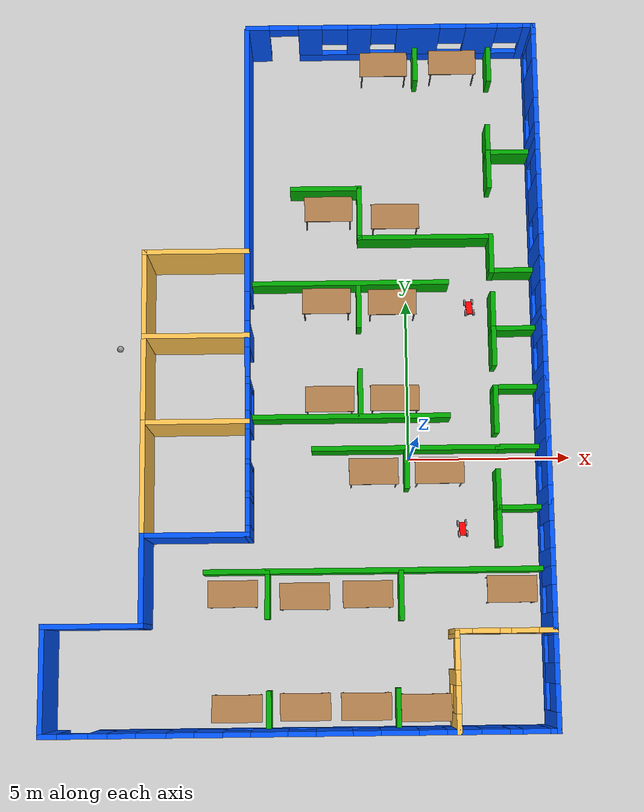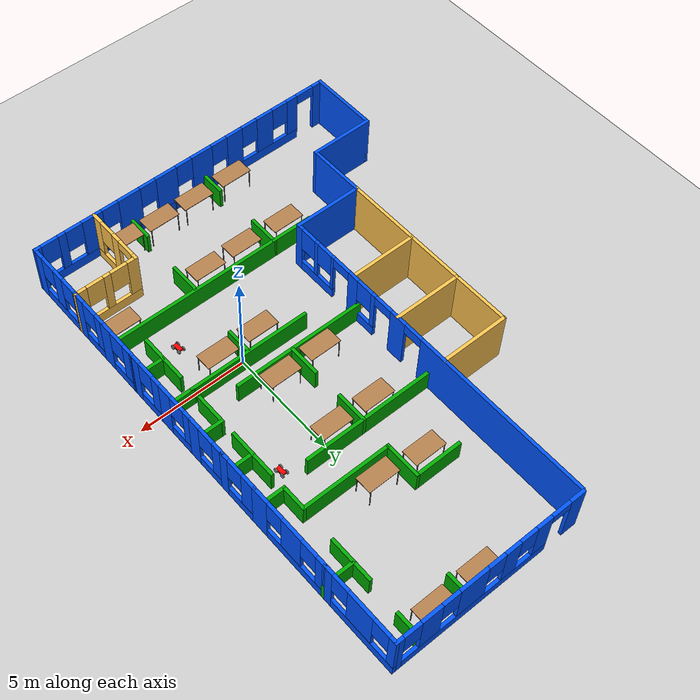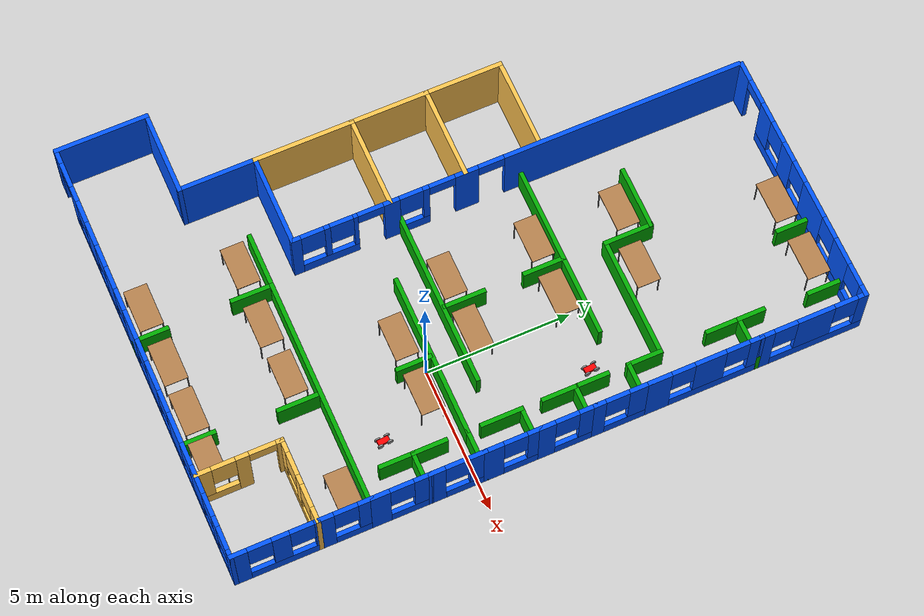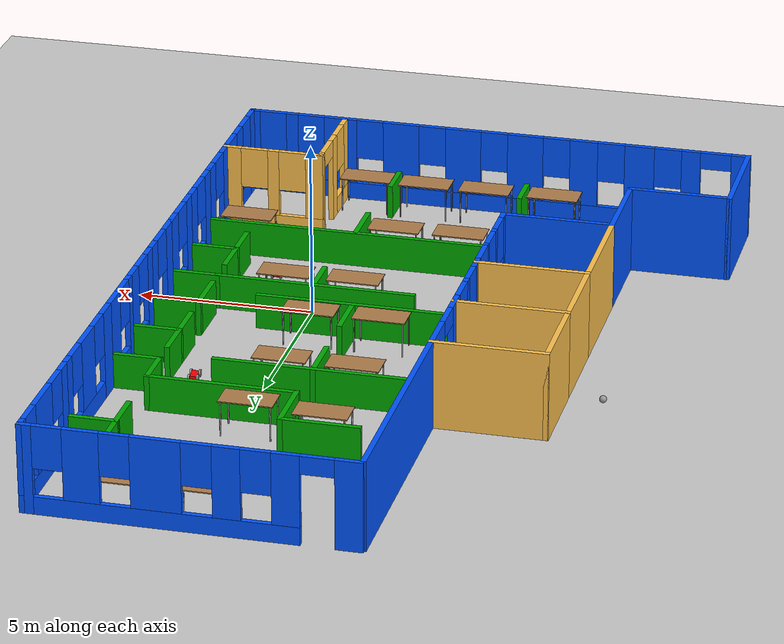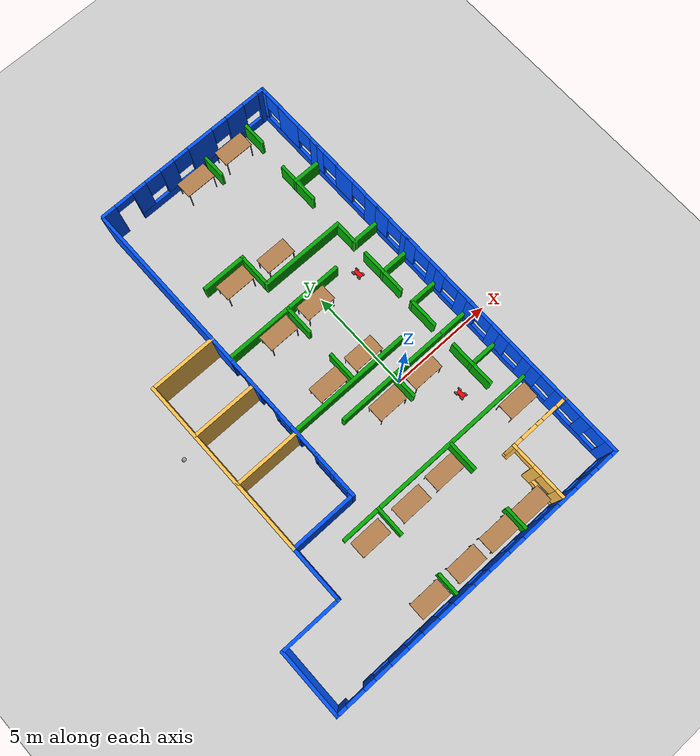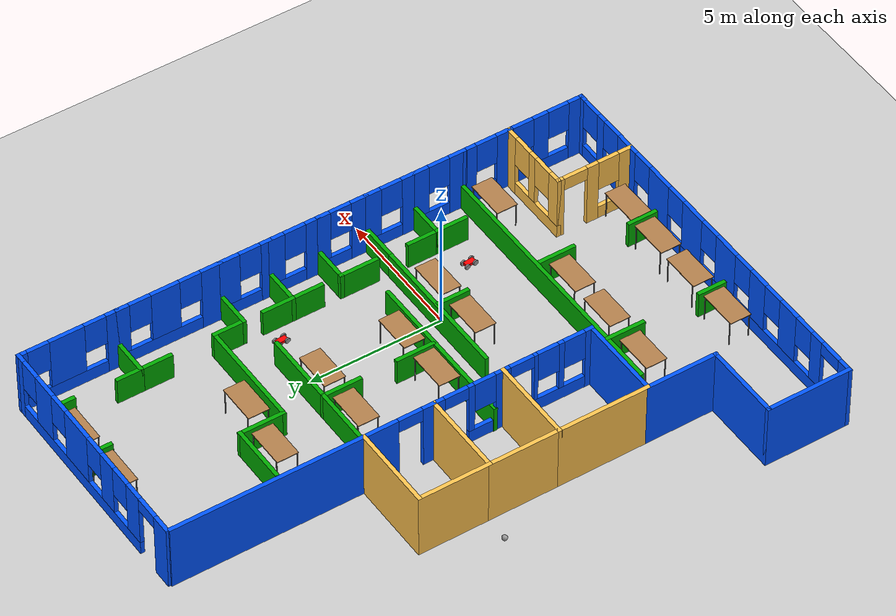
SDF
<sdf version="1.6">
 <world name="default">
  <light name="sun" type="directional">
   <pose>0 0 10 0 -0 0</pose>
   <diffuse>0.8 0.8 0.8 1</diffuse>
   <specular>0.2 0.2 0.2 1</specular>
   <attenuation>
    <range>1000</range>
    <constant>0.9</constant>
    <linear>0.01</linear>
    <quadratic>0.001</quadratic>
   </attenuation>
   <direction>-0.5 0.1 -0.9</direction>
  </light>
  <model name="ground_plane">
   <static>1</static>
   <link name="link">
    <collision name="collision">
     <geometry><plane><normal>0 0 1</normal><size>100 100</size></plane></geometry>
     <surface><friction><ode><mu>100</mu><mu2>50</mu2></ode></friction></surface>
    </collision>
    <visual name="visual">
     <cast_shadows>0</cast_shadows>
     <geometry><plane><normal>0 0 1</normal><size>100 100</size></plane></geometry>
     <material>
      <script><uri>file://media/materials/scripts/gazebo.material</uri><name>Gazebo/Grey</name></script>
     </material>
    </visual>
   </link>
  </model>
  <gravity>0 0 -9.8</gravity>
  <magnetic_field>6e-06 2.3e-05 -4.2e-05</magnetic_field>
  <atmosphere type="adiabatic"/>
  <physics name="default_physics" default="0" type="ode">
   <max_step_size>0.001</max_step_size>
   <real_time_factor>1</real_time_factor>
   <real_time_update_rate>1000</real_time_update_rate>
  </physics>
  <scene><ambient>0.4 0.4 0.4 1</ambient><background>0.7 0.7 0.7 1</background><shadows>1</shadows></scene>
  <spherical_coordinates>
   <surface_model>EARTH_WGS84</surface_model>
   <latitude_deg>0</latitude_deg>
   <longitude_deg>0</longitude_deg>
   <elevation>0</elevation>
   <heading_deg>0</heading_deg>
  </spherical_coordinates>
  <model name="AMG">
   <pose>-3.41412 2.5474 0 0 -0 0</pose>
   <link name="Wall_0">
    <pose>-0.000145 -10.6988 0 0 -0 3.14159</pose>
    <visual name="Wall_0_Visual_0">
     <pose>-7.33634 0 1.25 0 -0 0</pose>
     <geometry><box><size>0.327324 0.15 2.5</size></box></geometry>
     <material>
      <script><uri>file://media/materials/scripts/gazebo.material</uri><name>Gazebo/Grey</name></script>
      <ambient>0 0.333333 1 1</ambient>
     </material>
     <meta><layer>0</layer></meta>
    </visual>
    <collision name="Wall_0_Collision_0">
     <geometry><box><size>0.327324 0.15 2.5</size></box></geometry>
     <pose>-7.33634 0 1.25 0 -0 0</pose>
    </collision>
    <visual name="Wall_0_Visual_1">
     <pose>7.22017 0 1.25 0 -0 0</pose>
     <geometry><box><size>0.559664 0.15 2.5</size></box></geometry>
     <material>
      <script><uri>file://media/materials/scripts/gazebo.material</uri><name>Gazebo/Grey</name></script>
      <ambient>0 0.333333 1 1</ambient>
     </material>
     <meta><layer>0</layer></meta>
    </visual>
    <collision name="Wall_0_Collision_1">
     <geometry><box><size>0.559664 0.15 2.5</size></box></geometry>
     <pose>7.22017 0 1.25 0 -0 0</pose>
    </collision>
    <visual name="Wall_0_Visual_2">
     <pose>-0.56617 0 0.25 0 -0 0</pose>
     <geometry><box><size>13.213 0.15 0.5</size></box></geometry>
     <material>
      <script><uri>file://media/materials/scripts/gazebo.material</uri><name>Gazebo/Grey</name></script>
      <ambient>0 0.333333 1 1</ambient>
     </material>
     <meta><layer>0</layer></meta>
    </visual>
    <collision name="Wall_0_Collision_2">
     <geometry><box><size>13.213 0.15 0.5</size></box></geometry>
     <pose>-0.56617 0 0.25 0 -0 0</pose>
    </collision>
    <visual name="Wall_0_Visual_3">
     <pose>-6.1917 0 1.5 0 -0 0</pose>
     <geometry><box><size>0.361953 0.15 2</size></box></geometry>
     <material>
      <script><uri>file://media/materials/scripts/gazebo.material</uri><name>Gazebo/Grey</name></script>
      <ambient>0 0.333333 1 1</ambient>
     </material>
     <meta><layer>0</layer></meta>
    </visual>
    <collision name="Wall_0_Collision_3">
     <geometry><box><size>0.361953 0.15 2</size></box></geometry>
     <pose>-6.1917 0 1.5 0 -0 0</pose>
    </collision>
    <visual name="Wall_0_Visual_4">
     <pose>-4.71592 0 1.5 0 -0 0</pose>
     <geometry><box><size>0.989614 0.15 2</size></box></geometry>
     <material>
      <script><uri>file://media/materials/scripts/gazebo.material</uri><name>Gazebo/Grey</name></script>
      <ambient>0 0.333333 1 1</ambient>
     </material>
     <meta><layer>0</layer></meta>
    </visual>
    <collision name="Wall_0_Collision_4">
     <geometry><box><size>0.989614 0.15 2</size></box></geometry>
     <pose>-4.71592 0 1.5 0 -0 0</pose>
    </collision>
    <visual name="Wall_0_Visual_5">
     <pose>-2.8768 0 1.5 0 -0 0</pose>
     <geometry><box><size>1.08861 0.15 2</size></box></geometry>
     <material>
      <script><uri>file://media/materials/scripts/gazebo.material</uri><name>Gazebo/Grey</name></script>
      <ambient>0 0.333333 1 1</ambient>
     </material>
     <meta><layer>0</layer></meta>
    </visual>
    <collision name="Wall_0_Collision_5">
     <geometry><box><size>1.08861 0.15 2</size></box></geometry>
     <pose>-2.8768 0 1.5 0 -0 0</pose>
    </collision>
    <visual name="Wall_0_Visual_6">
     <pose>-1.00149 0 1.5 0 -0 0</pose>
     <geometry><box><size>1.06201 0.15 2</size></box></geometry>
     <material>
      <script><uri>file://media/materials/scripts/gazebo.material</uri><name>Gazebo/Grey</name></script>
      <ambient>0 0.333333 1 1</ambient>
     </material>
     <meta><layer>0</layer></meta>
    </visual>
    <collision name="Wall_0_Collision_6">
     <geometry><box><size>1.06201 0.15 2</size></box></geometry>
     <pose>-1.00149 0 1.5 0 -0 0</pose>
    </collision>
    <visual name="Wall_0_Visual_7">
     <pose>0.860526 0 1.5 0 -0 0</pose>
     <geometry><box><size>1.06201 0.15 2</size></box></geometry>
     <material>
      <script><uri>file://media/materials/scripts/gazebo.material</uri><name>Gazebo/Grey</name></script>
      <ambient>0 0.333333 1 1</ambient>
     </material>
     <meta><layer>0</layer></meta>
    </visual>
    <collision name="Wall_0_Collision_7">
     <geometry><box><size>1.06201 0.15 2</size></box></geometry>
     <pose>0.860526 0 1.5 0 -0 0</pose>
    </collision>
    <visual name="Wall_0_Visual_8">
     <pose>2.60284 0 1.5 0 -0 0</pose>
     <geometry><box><size>0.822612 0.15 2</size></box></geometry>
     <material>
      <script><uri>file://media/materials/scripts/gazebo.material</uri><name>Gazebo/Grey</name></script>
      <ambient>0 0.333333 1 1</ambient>
     </material>
     <meta><layer>0</layer></meta>
    </visual>
    <collision name="Wall_0_Collision_8">
     <geometry><box><size>0.822612 0.15 2</size></box></geometry>
     <pose>2.60284 0 1.5 0 -0 0</pose>
    </collision>
    <visual name="Wall_0_Visual_9">
     <pose>4.25205 0 1.5 0 -0 0</pose>
     <geometry><box><size>0.875812 0.15 2</size></box></geometry>
     <material>
      <script><uri>file://media/materials/scripts/gazebo.material</uri><name>Gazebo/Grey</name></script>
      <ambient>0 0.333333 1 1</ambient>
     </material>
     <meta><layer>0</layer></meta>
    </visual>
    <collision name="Wall_0_Collision_9">
     <geometry><box><size>0.875812 0.15 2</size></box></geometry>
     <pose>4.25205 0 1.5 0 -0 0</pose>
    </collision>
    <visual name="Wall_0_Visual_10">
     <pose>5.76515 0 1.5 0 -0 0</pose>
     <geometry><box><size>0.550378 0.15 2</size></box></geometry>
     <material>
      <script><uri>file://media/materials/scripts/gazebo.material</uri><name>Gazebo/Grey</name></script>
      <ambient>0 0.333333 1 1</ambient>
     </material>
     <meta><layer>0</layer></meta>
    </visual>
    <collision name="Wall_0_Collision_10">
     <geometry><box><size>0.550378 0.15 2</size></box></geometry>
     <pose>5.76515 0 1.5 0 -0 0</pose>
    </collision>
    <visual name="Wall_0_Visual_11">
     <pose>-6.77268 0 1.9 0 -0 0</pose>
     <geometry><box><size>0.8 0.15 1.2</size></box></geometry>
     <material>
      <script><uri>file://media/materials/scripts/gazebo.material</uri><name>Gazebo/Grey</name></script>
      <ambient>0 0.333333 1 1</ambient>
     </material>
     <meta><layer>0</layer></meta>
    </visual>
    <collision name="Wall_0_Collision_11">
     <geometry><box><size>0.8 0.15 1.2</size></box></geometry>
     <pose>-6.77268 0 1.9 0 -0 0</pose>
    </collision>
    <visual name="Wall_0_Visual_12">
     <pose>-5.61072 0 1.9 0 -0 0</pose>
     <geometry><box><size>0.8 0.15 1.2</size></box></geometry>
     <material>
      <script><uri>file://media/materials/scripts/gazebo.material</uri><name>Gazebo/Grey</name></script>
      <ambient>0 0.333333 1 1</ambient>
     </material>
     <meta><layer>0</layer></meta>
    </visual>
    <collision name="Wall_0_Collision_12">
     <geometry><box><size>0.8 0.15 1.2</size></box></geometry>
     <pose>-5.61072 0 1.9 0 -0 0</pose>
    </collision>
    <visual name="Wall_0_Visual_13">
     <pose>-3.82111 0 1.9 0 -0 0</pose>
     <geometry><box><size>0.8 0.15 1.2</size></box></geometry>
     <material>
      <script><uri>file://media/materials/scripts/gazebo.material</uri><name>Gazebo/Grey</name></script>
      <ambient>0 0.333333 1 1</ambient>
     </material>
     <meta><layer>0</layer></meta>
    </visual>
    <collision name="Wall_0_Collision_13">
     <geometry><box><size>0.8 0.15 1.2</size></box></geometry>
     <pose>-3.82111 0 1.9 0 -0 0</pose>
    </collision>
    <visual name="Wall_0_Visual_14">
     <pose>-1.9325 0 1.9 0 -0 0</pose>
     <geometry><box><size>0.8 0.15 1.2</size></box></geometry>
     <material>
      <script><uri>file://media/materials/scripts/gazebo.material</uri><name>Gazebo/Grey</name></script>
      <ambient>0 0.333333 1 1</ambient>
     </material>
     <meta><layer>0</layer></meta>
    </visual>
    <collision name="Wall_0_Collision_14">
     <geometry><box><size>0.8 0.15 1.2</size></box></geometry>
     <pose>-1.9325 0 1.9 0 -0 0</pose>
    </collision>
    <visual name="Wall_0_Visual_15">
     <pose>-0.070481 0 1.9 0 -0 0</pose>
     <geometry><box><size>0.8 0.15 1.2</size></box></geometry>
     <material>
      <script><uri>file://media/materials/scripts/gazebo.material</uri><name>Gazebo/Grey</name></script>
      <ambient>0 0.333333 1 1</ambient>
     </material>
     <meta><layer>0</layer></meta>
    </visual>
    <collision name="Wall_0_Collision_15">
     <geometry><box><size>0.8 0.15 1.2</size></box></geometry>
     <pose>-0.070481 0 1.9 0 -0 0</pose>
    </collision>
    <visual name="Wall_0_Visual_16">
     <pose>1.79153 0 1.9 0 -0 0</pose>
     <geometry><box><size>0.8 0.15 1.2</size></box></geometry>
     <material>
      <script><uri>file://media/materials/scripts/gazebo.material</uri><name>Gazebo/Grey</name></script>
      <ambient>0 0.333333 1 1</ambient>
     </material>
     <meta><layer>0</layer></meta>
    </visual>
    <collision name="Wall_0_Collision_16">
     <geometry><box><size>0.8 0.15 1.2</size></box></geometry>
     <pose>1.79153 0 1.9 0 -0 0</pose>
    </collision>
    <visual name="Wall_0_Visual_17">
     <pose>3.41414 0 1.9 0 -0 0</pose>
     <geometry><box><size>0.8 0.15 1.2</size></box></geometry>
     <material>
      <script><uri>file://media/materials/scripts/gazebo.material</uri><name>Gazebo/Grey</name></script>
      <ambient>0 0.333333 1 1</ambient>
     </material>
     <meta><layer>0</layer></meta>
    </visual>
    <collision name="Wall_0_Collision_17">
     <geometry><box><size>0.8 0.15 1.2</size></box></geometry>
     <pose>3.41414 0 1.9 0 -0 0</pose>
    </collision>
    <visual name="Wall_0_Visual_18">
     <pose>5.08996 0 1.9 0 -0 0</pose>
     <geometry><box><size>0.8 0.15 1.2</size></box></geometry>
     <material>
      <script><uri>file://media/materials/scripts/gazebo.material</uri><name>Gazebo/Grey</name></script>
      <ambient>0 0.333333 1 1</ambient>
     </material>
     <meta><layer>0</layer></meta>
    </visual>
    <collision name="Wall_0_Collision_18">
     <geometry><box><size>0.8 0.15 1.2</size></box></geometry>
     <pose>5.08996 0 1.9 0 -0 0</pose>
    </collision>
    <visual name="Wall_0_Visual_19">
     <pose>6.49034 0 2.25 0 -0 0</pose>
     <geometry><box><size>0.9 0.15 0.5</size></box></geometry>
     <material>
      <script><uri>file://media/materials/scripts/gazebo.material</uri><name>Gazebo/Grey</name></script>
      <ambient>0 0.333333 1 1</ambient>
     </material>
     <meta><layer>0</layer></meta>
    </visual>
    <collision name="Wall_0_Collision_19">
     <geometry><box><size>0.9 0.15 0.5</size></box></geometry>
     <pose>6.49034 0 2.25 0 -0 0</pose>
    </collision>
   </link>
   <link name="Wall_10">
    <collision name="Wall_10_Collision">
     <geometry><box><size>1.5 0.15 1</size></box></geometry>
     <pose>0 0 0.5 0 -0 0</pose>
    </collision>
    <visual name="Wall_10_Visual">
     <pose>0 0 0.5 0 -0 0</pose>
     <geometry><box><size>1.5 0.15 1</size></box></geometry>
     <material>
      <script><uri>file://media/materials/scripts/gazebo.material</uri><name>Gazebo/Grey</name></script>
      <ambient>0 0.666667 0 1</ambient>
     </material>
     <meta><layer>0</layer></meta>
    </visual>
    <pose>6.75014 -4.14841 0 0 -0 3.14159</pose>
   </link>
   <link name="Wall_101">
    <collision name="Wall_101_Collision">
     <geometry><box><size>1.25 0.15 1</size></box></geometry>
     <pose>0 0 0.5 0 -0 0</pose>
    </collision>
    <visual name="Wall_101_Visual">
     <pose>0 0 0.5 0 -0 0</pose>
     <geometry><box><size>1.25 0.15 1</size></box></geometry>
     <material>
      <script><uri>file://media/materials/scripts/gazebo.material</uri><name>Gazebo/Grey</name></script>
      <ambient>0 0.666667 0 1</ambient>
     </material>
     <meta><layer>0</layer></meta>
    </visual>
    <pose>6.17014 10.0946 0 0 0 -1.5708</pose>
   </link>
   <link name="Wall_103">
    <collision name="Wall_103_Collision">
     <geometry><box><size>1 0.15 1</size></box></geometry>
     <pose>0 0 0.5 0 -0 0</pose>
    </collision>
    <visual name="Wall_103_Visual">
     <pose>0 0 0.5 0 -0 0</pose>
     <geometry><box><size>1 0.15 1</size></box></geometry>
     <material>
      <script><uri>file://media/materials/scripts/gazebo.material</uri><name>Gazebo/Grey</name></script>
      <ambient>0 0.666667 0 1</ambient>
     </material>
     <meta><layer>0</layer></meta>
    </visual>
    <pose>6.07514 7.5266 0 0 -0 1.5708</pose>
   </link>
   <link name="Wall_105">
    <collision name="Wall_105_Collision">
     <geometry><box><size>1.25 0.15 1</size></box></geometry>
     <pose>0 0 0.5 0 -0 0</pose>
    </collision>
    <visual name="Wall_105_Visual">
     <pose>0 0 0.5 0 -0 0</pose>
     <geometry><box><size>1.25 0.15 1</size></box></geometry>
     <material>
      <script><uri>file://media/materials/scripts/gazebo.material</uri><name>Gazebo/Grey</name></script>
      <ambient>0 0.666667 0 1</ambient>
     </material>
     <meta><layer>0</layer></meta>
    </visual>
    <pose>3.82113 10.1446 0 0 0 -1.5708</pose>
   </link>
   <link name="Wall_107">
    <collision name="Wall_107_Collision">
     <geometry><box><size>8.5 0.15 1</size></box></geometry>
     <pose>0 0 0.5 0 -0 0</pose>
    </collision>
    <visual name="Wall_107_Visual">
     <pose>0 0 0.5 0 -0 0</pose>
     <geometry><box><size>8.5 0.15 1</size></box></geometry>
     <material>
      <script><uri>file://media/materials/scripts/gazebo.material</uri><name>Gazebo/Grey</name></script>
      <ambient>0 0.666667 0 1</ambient>
     </material>
     <meta><layer>0</layer></meta>
    </visual>
    <pose>3.21014 -5.9984 0 0 -0 0</pose>
   </link>
   <link name="Wall_18">
    <collision name="Wall_18_Collision">
     <geometry><box><size>1.5 0.15 1</size></box></geometry>
     <pose>0 0 0.5 0 -0 0</pose>
    </collision>
    <visual name="Wall_18_Visual">
     <pose>0 0 0.5 0 -0 0</pose>
     <geometry><box><size>1.5 0.15 1</size></box></geometry>
     <material>
      <script><uri>file://media/materials/scripts/gazebo.material</uri><name>Gazebo/Grey</name></script>
      <ambient>0 0.666667 0 1</ambient>
     </material>
     <meta><layer>0</layer></meta>
    </visual>
    <pose>3.06514 -6.7504 0 0 0 -1.5708</pose>
   </link>
   <link name="Wall_2">
    <pose>7.42485 -9.27379 0 0 -0 1.5708</pose>
    <visual name="Wall_2_Visual_0">
     <pose>-1.19989 0 1.25 0 -0 0</pose>
     <geometry><box><size>0.600224 0.15 2.5</size></box></geometry>
     <material>
      <script><uri>file://media/materials/scripts/gazebo.material</uri><name>Gazebo/Grey</name></script>
      <ambient>0 0.333333 1 1</ambient>
     </material>
     <meta><layer>0</layer></meta>
    </visual>
    <collision name="Wall_2_Collision_0">
     <geometry><box><size>0.600224 0.15 2.5</size></box></geometry>
     <pose>-1.19989 0 1.25 0 -0 0</pose>
    </collision>
    <visual name="Wall_2_Visual_1">
     <pose>0.300112 0 0.25 0 -0 0</pose>
     <geometry><box><size>2.39978 0.15 0.5</size></box></geometry>
     <material>
      <script><uri>file://media/materials/scripts/gazebo.material</uri><name>Gazebo/Grey</name></script>
      <ambient>0 0.333333 1 1</ambient>
     </material>
     <meta><layer>0</layer></meta>
    </visual>
    <collision name="Wall_2_Collision_1">
     <geometry><box><size>2.39978 0.15 0.5</size></box></geometry>
     <pose>0.300112 0 0.25 0 -0 0</pose>
    </collision>
    <visual name="Wall_2_Visual_2">
     <pose>0.194142 0 1.5 0 -0 0</pose>
     <geometry><box><size>0.587836 0.15 2</size></box></geometry>
     <material>
      <script><uri>file://media/materials/scripts/gazebo.material</uri><name>Gazebo/Grey</name></script>
      <ambient>0 0.333333 1 1</ambient>
     </material>
     <meta><layer>0</layer></meta>
    </visual>
    <collision name="Wall_2_Collision_2">
     <geometry><box><size>0.587836 0.15 2</size></box></geometry>
     <pose>0.194142 0 1.5 0 -0 0</pose>
    </collision>
    <visual name="Wall_2_Visual_3">
     <pose>1.39403 0 1.5 0 -0 0</pose>
     <geometry><box><size>0.211939 0.15 2</size></box></geometry>
     <material>
      <script><uri>file://media/materials/scripts/gazebo.material</uri><name>Gazebo/Grey</name></script>
      <ambient>0 0.333333 1 1</ambient>
     </material>
     <meta><layer>0</layer></meta>
    </visual>
    <collision name="Wall_2_Collision_3">
     <geometry><box><size>0.211939 0.15 2</size></box></geometry>
     <pose>1.39403 0 1.5 0 -0 0</pose>
    </collision>
    <visual name="Wall_2_Visual_4">
     <pose>-0.499776 0 1.9 0 -0 0</pose>
     <geometry><box><size>0.8 0.15 1.2</size></box></geometry>
     <material>
      <script><uri>file://media/materials/scripts/gazebo.material</uri><name>Gazebo/Grey</name></script>
      <ambient>0 0.333333 1 1</ambient>
     </material>
     <meta><layer>0</layer></meta>
    </visual>
    <collision name="Wall_2_Collision_4">
     <geometry><box><size>0.8 0.15 1.2</size></box></geometry>
     <pose>-0.499776 0 1.9 0 -0 0</pose>
    </collision>
    <visual name="Wall_2_Visual_5">
     <pose>0.888061 0 1.9 0 -0 0</pose>
     <geometry><box><size>0.8 0.15 1.2</size></box></geometry>
     <material>
      <script><uri>file://media/materials/scripts/gazebo.material</uri><name>Gazebo/Grey</name></script>
      <ambient>0 0.333333 1 1</ambient>
     </material>
     <meta><layer>0</layer></meta>
    </visual>
    <collision name="Wall_2_Collision_5">
     <geometry><box><size>0.8 0.15 1.2</size></box></geometry>
     <pose>0.888061 0 1.9 0 -0 0</pose>
    </collision>
   </link>
   <link name="Wall_21">
    <collision name="Wall_21_Collision">
     <geometry><box><size>1.5 0.15 1</size></box></geometry>
     <pose>0 0 0.5 0 -0 0</pose>
    </collision>
    <visual name="Wall_21_Visual">
     <pose>0 0 0.5 0 -0 0</pose>
     <geometry><box><size>1.5 0.15 1</size></box></geometry>
     <material>
      <script><uri>file://media/materials/scripts/gazebo.material</uri><name>Gazebo/Grey</name></script>
      <ambient>0 0.666667 0 1</ambient>
     </material>
     <meta><layer>0</layer></meta>
    </visual>
    <pose>-0.969865 -6.6734 0 0 0 -1.5782</pose>
   </link>
   <link name="Wall_23">
    <collision name="Wall_23_Collision">
     <geometry><box><size>2.01028 0.15 1</size></box></geometry>
     <pose>0 0 0.5 0 -0 0</pose>
    </collision>
    <visual name="Wall_23_Visual">
     <pose>0 0 0.5 0 -0 0</pose>
     <geometry><box><size>2.01028 0.15 1</size></box></geometry>
     <material>
      <script><uri>file://media/materials/scripts/gazebo.material</uri><name>Gazebo/Grey</name></script>
      <ambient>0 0.666667 0 1</ambient>
     </material>
     <meta><layer>0</layer></meta>
    </visual>
    <pose>-1.89487 -5.9984 0 0 -0 3.14159</pose>
   </link>
   <link name="Wall_25">
    <collision name="Wall_25_Collision">
     <geometry><box><size>1.25 0.15 1</size></box></geometry>
     <pose>0 0 0.5 0 -0 0</pose>
    </collision>
    <visual name="Wall_25_Visual">
     <pose>0 0 0.5 0 -0 0</pose>
     <geometry><box><size>1.25 0.15 1</size></box></geometry>
     <material>
      <script><uri>file://media/materials/scripts/gazebo.material</uri><name>Gazebo/Grey</name></script>
      <ambient>0 0.666667 0 1</ambient>
     </material>
     <meta><layer>0</layer></meta>
    </visual>
    <pose>2.92213 -10.0984 0 0 -0 1.5708</pose>
   </link>
   <link name="Wall_27">
    <collision name="Wall_27_Collision">
     <geometry><box><size>1.25 0.15 1</size></box></geometry>
     <pose>0 0 0.5 0 -0 0</pose>
    </collision>
    <visual name="Wall_27_Visual">
     <pose>0 0 0.5 0 -0 0</pose>
     <geometry><box><size>1.25 0.15 1</size></box></geometry>
     <material>
      <script><uri>file://media/materials/scripts/gazebo.material</uri><name>Gazebo/Grey</name></script>
      <ambient>0 0.666667 0 1</ambient>
     </material>
     <meta><layer>0</layer></meta>
    </visual>
    <pose>-0.934865 -10.1514 0 0 -0 1.5708</pose>
   </link>
   <link name="Wall_29">
    <collision name="Wall_29_Collision">
     <geometry><box><size>3.25 0.15 2.5</size></box></geometry>
     <pose>0 0 1.25 0 -0 0</pose>
    </collision>
    <visual name="Wall_29_Visual">
     <pose>0 0 1.25 0 -0 0</pose>
     <geometry><box><size>3.25 0.15 2.5</size></box></geometry>
     <material>
      <script><uri>file://media/materials/scripts/gazebo.material</uri><name>Gazebo/Grey</name></script>
      <ambient>0 0.333333 1 1</ambient>
     </material>
     <meta><layer>0</layer></meta>
    </visual>
    <pose>-7.42514 -9.14879 0 0 -0 1.5708</pose>
   </link>
   <link name="Wall_3">
    <pose>5.99986 -7.84879 0 0 -0 3.14159</pose>
    <visual name="Wall_3_Visual_0">
     <pose>-1.22302 0 1.25 0 -0 0</pose>
     <geometry><box><size>0.553963 0.15 2.5</size></box></geometry>
     <material>
      <script><uri>file://media/materials/scripts/gazebo.material</uri><name>Gazebo/Grey</name></script>
      <ambient>1 0.764706 0.305882 1</ambient>
     </material>
     <meta><layer>0</layer></meta>
    </visual>
    <collision name="Wall_3_Collision_0">
     <geometry><box><size>0.553963 0.15 2.5</size></box></geometry>
     <pose>-1.22302 0 1.25 0 -0 0</pose>
    </collision>
    <visual name="Wall_3_Visual_1">
     <pose>0.276982 0 0.25 0 -0 0</pose>
     <geometry><box><size>2.44604 0.15 0.5</size></box></geometry>
     <material>
      <script><uri>file://media/materials/scripts/gazebo.material</uri><name>Gazebo/Grey</name></script>
      <ambient>1 0.764706 0.305882 1</ambient>
     </material>
     <meta><layer>0</layer></meta>
    </visual>
    <collision name="Wall_3_Collision_1">
     <geometry><box><size>2.44604 0.15 0.5</size></box></geometry>
     <pose>0.276982 0 0.25 0 -0 0</pose>
    </collision>
    <visual name="Wall_3_Visual_2">
     <pose>0.020663 0 1.5 0 -0 0</pose>
     <geometry><box><size>0.3334 0.15 2</size></box></geometry>
     <material>
      <script><uri>file://media/materials/scripts/gazebo.material</uri><name>Gazebo/Grey</name></script>
      <ambient>1 0.764706 0.305882 1</ambient>
     </material>
     <meta><layer>0</layer></meta>
    </visual>
    <collision name="Wall_3_Collision_2">
     <geometry><box><size>0.3334 0.15 2</size></box></geometry>
     <pose>0.020663 0 1.5 0 -0 0</pose>
    </collision>
    <visual name="Wall_3_Visual_3">
     <pose>1.24368 0 1.5 0 -0 0</pose>
     <geometry><box><size>0.512637 0.15 2</size></box></geometry>
     <material>
      <script><uri>file://media/materials/scripts/gazebo.material</uri><name>Gazebo/Grey</name></script>
      <ambient>1 0.764706 0.305882 1</ambient>
     </material>
     <meta><layer>0</layer></meta>
    </visual>
    <collision name="Wall_3_Collision_3">
     <geometry><box><size>0.512637 0.15 2</size></box></geometry>
     <pose>1.24368 0 1.5 0 -0 0</pose>
    </collision>
    <visual name="Wall_3_Visual_4">
     <pose>-0.546037 0 1.9 0 -0 0</pose>
     <geometry><box><size>0.8 0.15 1.2</size></box></geometry>
     <material>
      <script><uri>file://media/materials/scripts/gazebo.material</uri><name>Gazebo/Grey</name></script>
      <ambient>1 0.764706 0.305882 1</ambient>
     </material>
     <meta><layer>0</layer></meta>
    </visual>
    <collision name="Wall_3_Collision_4">
     <geometry><box><size>0.8 0.15 1.2</size></box></geometry>
     <pose>-0.546037 0 1.9 0 -0 0</pose>
    </collision>
    <visual name="Wall_3_Visual_5">
     <pose>0.587363 0 1.9 0 -0 0</pose>
     <geometry><box><size>0.8 0.15 1.2</size></box></geometry>
     <material>
      <script><uri>file://media/materials/scripts/gazebo.material</uri><name>Gazebo/Grey</name></script>
      <ambient>1 0.764706 0.305882 1</ambient>
     </material>
     <meta><layer>0</layer></meta>
    </visual>
    <collision name="Wall_3_Collision_5">
     <geometry><box><size>0.8 0.15 1.2</size></box></geometry>
     <pose>0.587363 0 1.9 0 -0 0</pose>
    </collision>
   </link>
   <link name="Wall_30">
    <collision name="Wall_30_Collision">
     <geometry><box><size>3 0.15 2.5</size></box></geometry>
     <pose>0 0 1.25 0 -0 0</pose>
    </collision>
    <visual name="Wall_30_Visual">
     <pose>0 0 1.25 0 -0 0</pose>
     <geometry><box><size>3 0.15 2.5</size></box></geometry>
     <material>
      <script><uri>file://media/materials/scripts/gazebo.material</uri><name>Gazebo/Grey</name></script>
      <ambient>0 0.333333 1 1</ambient>
     </material>
     <meta><layer>0</layer></meta>
    </visual>
    <pose>-6.00014 -7.59879 0 0 -0 0</pose>
   </link>
   <link name="Wall_31">
    <collision name="Wall_31_Collision">
     <geometry><box><size>2.75 0.15 2.5</size></box></geometry>
     <pose>0 0 1.25 0 -0 0</pose>
    </collision>
    <visual name="Wall_31_Visual">
     <pose>0 0 1.25 0 -0 0</pose>
     <geometry><box><size>2.75 0.15 2.5</size></box></geometry>
     <material>
      <script><uri>file://media/materials/scripts/gazebo.material</uri><name>Gazebo/Grey</name></script>
      <ambient>0 0.333333 1 1</ambient>
     </material>
     <meta><layer>0</layer></meta>
    </visual>
    <pose>-4.57515 -6.2988 0 0 -0 1.5708</pose>
   </link>
   <link name="Wall_36">
    <pose>7.42514 -3.22341 0 0 -0 1.5708</pose>
    <visual name="Wall_36_Visual_0">
     <pose>-0.710083 0 1.25 0 -0 0</pose>
     <geometry><box><size>0.579834 0.15 2.5</size></box></geometry>
     <material>
      <script><uri>file://media/materials/scripts/gazebo.material</uri><name>Gazebo/Grey</name></script>
      <ambient>0 0.333333 1 1</ambient>
     </material>
     <meta><layer>0</layer></meta>
    </visual>
    <collision name="Wall_36_Collision_0">
     <geometry><box><size>0.579834 0.15 2.5</size></box></geometry>
     <pose>-0.710083 0 1.25 0 -0 0</pose>
    </collision>
    <visual name="Wall_36_Visual_1">
     <pose>0.289917 0 0.25 0 -0 0</pose>
     <geometry><box><size>1.42017 0.15 0.5</size></box></geometry>
     <material>
      <script><uri>file://media/materials/scripts/gazebo.material</uri><name>Gazebo/Grey</name></script>
      <ambient>0 0.333333 1 1</ambient>
     </material>
     <meta><layer>0</layer></meta>
    </visual>
    <collision name="Wall_36_Collision_1">
     <geometry><box><size>1.42017 0.15 0.5</size></box></geometry>
     <pose>0.289917 0 0.25 0 -0 0</pose>
    </collision>
    <visual name="Wall_36_Visual_2">
     <pose>0.689917 0 1.5 0 -0 0</pose>
     <geometry><box><size>0.620166 0.15 2</size></box></geometry>
     <material>
      <script><uri>file://media/materials/scripts/gazebo.material</uri><name>Gazebo/Grey</name></script>
      <ambient>0 0.333333 1 1</ambient>
     </material>
     <meta><layer>0</layer></meta>
    </visual>
    <collision name="Wall_36_Collision_2">
     <geometry><box><size>0.620166 0.15 2</size></box></geometry>
     <pose>0.689917 0 1.5 0 -0 0</pose>
    </collision>
    <visual name="Wall_36_Visual_3">
     <pose>-0.020166 0 1.9 0 -0 0</pose>
     <geometry><box><size>0.8 0.15 1.2</size></box></geometry>
     <material>
      <script><uri>file://media/materials/scripts/gazebo.material</uri><name>Gazebo/Grey</name></script>
      <ambient>0 0.333333 1 1</ambient>
     </material>
     <meta><layer>0</layer></meta>
    </visual>
    <collision name="Wall_36_Collision_3">
     <geometry><box><size>0.8 0.15 1.2</size></box></geometry>
     <pose>-0.020166 0 1.9 0 -0 0</pose>
    </collision>
   </link>
   <link name="Wall_37">
    <collision name="Wall_37_Collision">
     <geometry><box><size>1.5 0.15 1</size></box></geometry>
     <pose>0 0 0.5 0 -0 0</pose>
    </collision>
    <visual name="Wall_37_Visual">
     <pose>0 0 0.5 0 -0 0</pose>
     <geometry><box><size>1.5 0.15 1</size></box></geometry>
     <material>
      <script><uri>file://media/materials/scripts/gazebo.material</uri><name>Gazebo/Grey</name></script>
      <ambient>0 0.666667 0 1</ambient>
     </material>
     <meta><layer>0</layer></meta>
    </visual>
    <pose>6.75014 -2.2984 0 0 -0 3.14159</pose>
   </link>
   <link name="Wall_39">
    <collision name="Wall_39_Collision">
     <geometry><box><size>1.25 0.15 1</size></box></geometry>
     <pose>0 0 0.5 0 -0 0</pose>
    </collision>
    <visual name="Wall_39_Visual">
     <pose>0 0 0.5 0 -0 0</pose>
     <geometry><box><size>1.25 0.15 1</size></box></geometry>
     <material>
      <script><uri>file://media/materials/scripts/gazebo.material</uri><name>Gazebo/Grey</name></script>
      <ambient>0 0.666667 0 1</ambient>
     </material>
     <meta><layer>0</layer></meta>
    </visual>
    <pose>6.07514 -3.59841 0 0 -0 1.5708</pose>
   </link>
   <link name="Wall_4">
    <pose>4.57486 -9.27379 0 0 0 -1.5708</pose>
    <visual name="Wall_4_Visual_0">
     <pose>-1.3612 0 1.25 0 -0 0</pose>
     <geometry><box><size>0.277592 0.15 2.5</size></box></geometry>
     <material>
      <script><uri>file://media/materials/scripts/gazebo.material</uri><name>Gazebo/Grey</name></script>
      <ambient>1 0.764706 0.305882 1</ambient>
     </material>
     <meta><layer>0</layer></meta>
    </visual>
    <collision name="Wall_4_Collision_0">
     <geometry><box><size>0.277592 0.15 2.5</size></box></geometry>
     <pose>-1.3612 0 1.25 0 -0 0</pose>
    </collision>
    <visual name="Wall_4_Visual_1">
     <pose>-0.099751 0 1.25 0 -0 0</pose>
     <geometry><box><size>0.445314 0.15 2.5</size></box></geometry>
     <material>
      <script><uri>file://media/materials/scripts/gazebo.material</uri><name>Gazebo/Grey</name></script>
      <ambient>1 0.764706 0.305882 1</ambient>
     </material>
     <meta><layer>0</layer></meta>
    </visual>
    <collision name="Wall_4_Collision_1">
     <geometry><box><size>0.445314 0.15 2.5</size></box></geometry>
     <pose>-0.099751 0 1.25 0 -0 0</pose>
    </collision>
    <visual name="Wall_4_Visual_2">
     <pose>0.811453 0 0.25 0 -0 0</pose>
     <geometry><box><size>1.37709 0.15 0.5</size></box></geometry>
     <material>
      <script><uri>file://media/materials/scripts/gazebo.material</uri><name>Gazebo/Grey</name></script>
      <ambient>1 0.764706 0.305882 1</ambient>
     </material>
     <meta><layer>0</layer></meta>
    </visual>
    <collision name="Wall_4_Collision_2">
     <geometry><box><size>1.37709 0.15 0.5</size></box></geometry>
     <pose>0.811453 0 0.25 0 -0 0</pose>
    </collision>
    <visual name="Wall_4_Visual_3">
     <pose>1.21145 0 1.5 0 -0 0</pose>
     <geometry><box><size>0.577094 0.15 2</size></box></geometry>
     <material>
      <script><uri>file://media/materials/scripts/gazebo.material</uri><name>Gazebo/Grey</name></script>
      <ambient>1 0.764706 0.305882 1</ambient>
     </material>
     <meta><layer>0</layer></meta>
    </visual>
    <collision name="Wall_4_Collision_3">
     <geometry><box><size>0.577094 0.15 2</size></box></geometry>
     <pose>1.21145 0 1.5 0 -0 0</pose>
    </collision>
    <visual name="Wall_4_Visual_4">
     <pose>0.522906 0 1.9 0 -0 0</pose>
     <geometry><box><size>0.8 0.15 1.2</size></box></geometry>
     <material>
      <script><uri>file://media/materials/scripts/gazebo.material</uri><name>Gazebo/Grey</name></script>
      <ambient>1 0.764706 0.305882 1</ambient>
     </material>
     <meta><layer>0</layer></meta>
    </visual>
    <collision name="Wall_4_Collision_4">
     <geometry><box><size>0.8 0.15 1.2</size></box></geometry>
     <pose>0.522906 0 1.9 0 -0 0</pose>
    </collision>
    <visual name="Wall_4_Visual_5">
     <pose>-0.772408 0 2.25 0 -0 0</pose>
     <geometry><box><size>0.9 0.15 0.5</size></box></geometry>
     <material>
      <script><uri>file://media/materials/scripts/gazebo.material</uri><name>Gazebo/Grey</name></script>
      <ambient>1 0.764706 0.305882 1</ambient>
     </material>
     <meta><layer>0</layer></meta>
    </visual>
    <collision name="Wall_4_Collision_5">
     <geometry><box><size>0.9 0.15 0.5</size></box></geometry>
     <pose>-0.772408 0 2.25 0 -0 0</pose>
    </collision>
   </link>
   <link name="Wall_43">
    <collision name="Wall_43_Collision">
     <geometry><box><size>1.25 0.15 1</size></box></geometry>
     <pose>0 0 0.5 0 -0 0</pose>
    </collision>
    <visual name="Wall_43_Visual">
     <pose>0 0 0.5 0 -0 0</pose>
     <geometry><box><size>1.25 0.15 1</size></box></geometry>
     <material>
      <script><uri>file://media/materials/scripts/gazebo.material</uri><name>Gazebo/Grey</name></script>
      <ambient>0 0.666667 0 1</ambient>
     </material>
     <meta><layer>0</layer></meta>
    </visual>
    <pose>6.07514 -4.69841 0 0 0 -1.5708</pose>
   </link>
   <link name="Wall_45">
    <pose>7.42514 -1.3734 0 0 -0 1.5708</pose>
    <visual name="Wall_45_Visual_0">
     <pose>-0.657384 0 1.25 0 -0 0</pose>
     <geometry><box><size>0.685231 0.15 2.5</size></box></geometry>
     <material>
      <script><uri>file://media/materials/scripts/gazebo.material</uri><name>Gazebo/Grey</name></script>
      <ambient>0 0.333333 1 1</ambient>
     </material>
     <meta><layer>0</layer></meta>
    </visual>
    <collision name="Wall_45_Collision_0">
     <geometry><box><size>0.685231 0.15 2.5</size></box></geometry>
     <pose>-0.657384 0 1.25 0 -0 0</pose>
    </collision>
    <visual name="Wall_45_Visual_1">
     <pose>0.342616 0 0.25 0 -0 0</pose>
     <geometry><box><size>1.31477 0.15 0.5</size></box></geometry>
     <material>
      <script><uri>file://media/materials/scripts/gazebo.material</uri><name>Gazebo/Grey</name></script>
      <ambient>0 0.333333 1 1</ambient>
     </material>
     <meta><layer>0</layer></meta>
    </visual>
    <collision name="Wall_45_Collision_1">
     <geometry><box><size>1.31477 0.15 0.5</size></box></geometry>
     <pose>0.342616 0 0.25 0 -0 0</pose>
    </collision>
    <visual name="Wall_45_Visual_2">
     <pose>0.742616 0 1.5 0 -0 0</pose>
     <geometry><box><size>0.514769 0.15 2</size></box></geometry>
     <material>
      <script><uri>file://media/materials/scripts/gazebo.material</uri><name>Gazebo/Grey</name></script>
      <ambient>0 0.333333 1 1</ambient>
     </material>
     <meta><layer>0</layer></meta>
    </visual>
    <collision name="Wall_45_Collision_2">
     <geometry><box><size>0.514769 0.15 2</size></box></geometry>
     <pose>0.742616 0 1.5 0 -0 0</pose>
    </collision>
    <visual name="Wall_45_Visual_3">
     <pose>0.085231 0 1.9 0 -0 0</pose>
     <geometry><box><size>0.8 0.15 1.2</size></box></geometry>
     <material>
      <script><uri>file://media/materials/scripts/gazebo.material</uri><name>Gazebo/Grey</name></script>
      <ambient>0 0.333333 1 1</ambient>
     </material>
     <meta><layer>0</layer></meta>
    </visual>
    <collision name="Wall_45_Collision_3">
     <geometry><box><size>0.8 0.15 1.2</size></box></geometry>
     <pose>0.085231 0 1.9 0 -0 0</pose>
    </collision>
   </link>
   <link name="Wall_46">
    <collision name="Wall_46_Collision">
     <geometry><box><size>1.5 0.15 1</size></box></geometry>
     <pose>0 0 0.5 0 -0 0</pose>
    </collision>
    <visual name="Wall_46_Visual">
     <pose>0 0 0.5 0 -0 0</pose>
     <geometry><box><size>1.5 0.15 1</size></box></geometry>
     <material>
      <script><uri>file://media/materials/scripts/gazebo.material</uri><name>Gazebo/Grey</name></script>
      <ambient>0 0.666667 0 1</ambient>
     </material>
     <meta><layer>0</layer></meta>
    </visual>
    <pose>6.75014 -0.448405 0 0 -0 3.14159</pose>
   </link>
   <link name="Wall_47">
    <collision name="Wall_47_Collision">
     <geometry><box><size>1.5 0.15 1</size></box></geometry>
     <pose>0 0 0.5 0 -0 0</pose>
    </collision>
    <visual name="Wall_47_Visual">
     <pose>0 0 0.5 0 -0 0</pose>
     <geometry><box><size>1.5 0.15 1</size></box></geometry>
     <material>
      <script><uri>file://media/materials/scripts/gazebo.material</uri><name>Gazebo/Grey</name></script>
      <ambient>0 0.666667 0 1</ambient>
     </material>
     <meta><layer>0</layer></meta>
    </visual>
    <pose>6.07514 -1.1234 0 0 0 -1.5708</pose>
   </link>
   <link name="Wall_51">
    <collision name="Wall_51_Collision">
     <geometry><box><size>3.25 0.15 2.5</size></box></geometry>
     <pose>0 0 1.25 0 -0 0</pose>
    </collision>
    <visual name="Wall_51_Visual">
     <pose>0 0 1.25 0 -0 0</pose>
     <geometry><box><size>3.25 0.15 2.5</size></box></geometry>
     <material>
      <script><uri>file://media/materials/scripts/gazebo.material</uri><name>Gazebo/Grey</name></script>
      <ambient>0 0.333333 1 1</ambient>
     </material>
     <meta><layer>0</layer></meta>
    </visual>
    <pose>-3.02515 -4.9988 0 0 -0 0</pose>
   </link>
   <link name="Wall_55">
    <pose>7.42514 0.476595 0 0 -0 1.5708</pose>
    <visual name="Wall_55_Visual_0">
     <pose>-0.710563 0 1.25 0 -0 0</pose>
     <geometry><box><size>0.578874 0.15 2.5</size></box></geometry>
     <material>
      <script><uri>file://media/materials/scripts/gazebo.material</uri><name>Gazebo/Grey</name></script>
      <ambient>0 0.333333 1 1</ambient>
     </material>
     <meta><layer>0</layer></meta>
    </visual>
    <collision name="Wall_55_Collision_0">
     <geometry><box><size>0.578874 0.15 2.5</size></box></geometry>
     <pose>-0.710563 0 1.25 0 -0 0</pose>
    </collision>
    <visual name="Wall_55_Visual_1">
     <pose>0.289437 0 0.25 0 -0 0</pose>
     <geometry><box><size>1.42113 0.15 0.5</size></box></geometry>
     <material>
      <script><uri>file://media/materials/scripts/gazebo.material</uri><name>Gazebo/Grey</name></script>
      <ambient>0 0.333333 1 1</ambient>
     </material>
     <meta><layer>0</layer></meta>
    </visual>
    <collision name="Wall_55_Collision_1">
     <geometry><box><size>1.42113 0.15 0.5</size></box></geometry>
     <pose>0.289437 0 0.25 0 -0 0</pose>
    </collision>
    <visual name="Wall_55_Visual_2">
     <pose>0.689437 0 1.5 0 -0 0</pose>
     <geometry><box><size>0.621126 0.15 2</size></box></geometry>
     <material>
      <script><uri>file://media/materials/scripts/gazebo.material</uri><name>Gazebo/Grey</name></script>
      <ambient>0 0.333333 1 1</ambient>
     </material>
     <meta><layer>0</layer></meta>
    </visual>
    <collision name="Wall_55_Collision_2">
     <geometry><box><size>0.621126 0.15 2</size></box></geometry>
     <pose>0.689437 0 1.5 0 -0 0</pose>
    </collision>
    <visual name="Wall_55_Visual_3">
     <pose>-0.021126 0 1.9 0 -0 0</pose>
     <geometry><box><size>0.8 0.15 1.2</size></box></geometry>
     <material>
      <script><uri>file://media/materials/scripts/gazebo.material</uri><name>Gazebo/Grey</name></script>
      <ambient>0 0.333333 1 1</ambient>
     </material>
     <meta><layer>0</layer></meta>
    </visual>
    <collision name="Wall_55_Collision_3">
     <geometry><box><size>0.8 0.15 1.2</size></box></geometry>
     <pose>-0.021126 0 1.9 0 -0 0</pose>
    </collision>
   </link>
   <link name="Wall_56">
    <collision name="Wall_56_Collision">
     <geometry><box><size>1.5 0.15 1</size></box></geometry>
     <pose>0 0 0.5 0 -0 0</pose>
    </collision>
    <visual name="Wall_56_Visual">
     <pose>0 0 0.5 0 -0 0</pose>
     <geometry><box><size>1.5 0.15 1</size></box></geometry>
     <material>
      <script><uri>file://media/materials/scripts/gazebo.material</uri><name>Gazebo/Grey</name></script>
      <ambient>0 0.666667 0 1</ambient>
     </material>
     <meta><layer>0</layer></meta>
    </visual>
    <pose>6.75014 1.40159 0 0 -0 3.14159</pose>
   </link>
   <link name="Wall_57">
    <collision name="Wall_57_Collision">
     <geometry><box><size>1.25 0.15 1</size></box></geometry>
     <pose>0 0 0.5 0 -0 0</pose>
    </collision>
    <visual name="Wall_57_Visual">
     <pose>0 0 0.5 0 -0 0</pose>
     <geometry><box><size>1.25 0.15 1</size></box></geometry>
     <material>
      <script><uri>file://media/materials/scripts/gazebo.material</uri><name>Gazebo/Grey</name></script>
      <ambient>0 0.666667 0 1</ambient>
     </material>
     <meta><layer>0</layer></meta>
    </visual>
    <pose>6.07514 0.851595 0 0 0 -1.5708</pose>
   </link>
   <link name="Wall_59">
    <collision name="Wall_59_Collision">
     <geometry><box><size>1.25 0.15 1</size></box></geometry>
     <pose>0 0 0.5 0 -0 0</pose>
    </collision>
    <visual name="Wall_59_Visual">
     <pose>0 0 0.5 0 -0 0</pose>
     <geometry><box><size>1.25 0.15 1</size></box></geometry>
     <material>
      <script><uri>file://media/materials/scripts/gazebo.material</uri><name>Gazebo/Grey</name></script>
      <ambient>0 0.666667 0 1</ambient>
     </material>
     <meta><layer>0</layer></meta>
    </visual>
    <pose>6.07514 1.95159 0 0 -0 1.5708</pose>
   </link>
   <link name="Wall_6">
    <pose>7.42485 -6.9637 0 0 -0 1.5708</pose>
    <visual name="Wall_6_Visual_0">
     <pose>-0.668909 0 1.25 0 -0 0</pose>
     <geometry><box><size>0.582382 0.15 2.5</size></box></geometry>
     <material>
      <script><uri>file://media/materials/scripts/gazebo.material</uri><name>Gazebo/Grey</name></script>
      <ambient>0 0.333333 1 1</ambient>
     </material>
     <meta><layer>0</layer></meta>
    </visual>
    <collision name="Wall_6_Collision_0">
     <geometry><box><size>0.582382 0.15 2.5</size></box></geometry>
     <pose>-0.668909 0 1.25 0 -0 0</pose>
    </collision>
    <visual name="Wall_6_Visual_1">
     <pose>0.291191 0 0.25 0 -0 0</pose>
     <geometry><box><size>1.33782 0.15 0.5</size></box></geometry>
     <material>
      <script><uri>file://media/materials/scripts/gazebo.material</uri><name>Gazebo/Grey</name></script>
      <ambient>0 0.333333 1 1</ambient>
     </material>
     <meta><layer>0</layer></meta>
    </visual>
    <collision name="Wall_6_Collision_1">
     <geometry><box><size>1.33782 0.15 0.5</size></box></geometry>
     <pose>0.291191 0 0.25 0 -0 0</pose>
    </collision>
    <visual name="Wall_6_Visual_2">
     <pose>0.691191 0 1.5 0 -0 0</pose>
     <geometry><box><size>0.537817 0.15 2</size></box></geometry>
     <material>
      <script><uri>file://media/materials/scripts/gazebo.material</uri><name>Gazebo/Grey</name></script>
      <ambient>0 0.333333 1 1</ambient>
     </material>
     <meta><layer>0</layer></meta>
    </visual>
    <collision name="Wall_6_Collision_2">
     <geometry><box><size>0.537817 0.15 2</size></box></geometry>
     <pose>0.691191 0 1.5 0 -0 0</pose>
    </collision>
    <visual name="Wall_6_Visual_3">
     <pose>0.022283 0 1.9 0 -0 0</pose>
     <geometry><box><size>0.8 0.15 1.2</size></box></geometry>
     <material>
      <script><uri>file://media/materials/scripts/gazebo.material</uri><name>Gazebo/Grey</name></script>
      <ambient>0 0.333333 1 1</ambient>
     </material>
     <meta><layer>0</layer></meta>
    </visual>
    <collision name="Wall_6_Collision_3">
     <geometry><box><size>0.8 0.15 1.2</size></box></geometry>
     <pose>0.022283 0 1.9 0 -0 0</pose>
    </collision>
   </link>
   <link name="Wall_61">
    <pose>7.42514 2.3266 0 0 -0 1.5708</pose>
    <visual name="Wall_61_Visual_0">
     <pose>-0.785841 0 1.25 0 -0 0</pose>
     <geometry><box><size>0.428317 0.15 2.5</size></box></geometry>
     <material>
      <script><uri>file://media/materials/scripts/gazebo.material</uri><name>Gazebo/Grey</name></script>
      <ambient>0 0.333333 1 1</ambient>
     </material>
     <meta><layer>0</layer></meta>
    </visual>
    <collision name="Wall_61_Collision_0">
     <geometry><box><size>0.428317 0.15 2.5</size></box></geometry>
     <pose>-0.785841 0 1.25 0 -0 0</pose>
    </collision>
    <visual name="Wall_61_Visual_1">
     <pose>0.214159 0 0.25 0 -0 0</pose>
     <geometry><box><size>1.57168 0.15 0.5</size></box></geometry>
     <material>
      <script><uri>file://media/materials/scripts/gazebo.material</uri><name>Gazebo/Grey</name></script>
      <ambient>0 0.333333 1 1</ambient>
     </material>
     <meta><layer>0</layer></meta>
    </visual>
    <collision name="Wall_61_Collision_1">
     <geometry><box><size>1.57168 0.15 0.5</size></box></geometry>
     <pose>0.214159 0 0.25 0 -0 0</pose>
    </collision>
    <visual name="Wall_61_Visual_2">
     <pose>0.614159 0 1.5 0 -0 0</pose>
     <geometry><box><size>0.771683 0.15 2</size></box></geometry>
     <material>
      <script><uri>file://media/materials/scripts/gazebo.material</uri><name>Gazebo/Grey</name></script>
      <ambient>0 0.333333 1 1</ambient>
     </material>
     <meta><layer>0</layer></meta>
    </visual>
    <collision name="Wall_61_Collision_2">
     <geometry><box><size>0.771683 0.15 2</size></box></geometry>
     <pose>0.614159 0 1.5 0 -0 0</pose>
    </collision>
    <visual name="Wall_61_Visual_3">
     <pose>-0.171683 0 1.9 0 -0 0</pose>
     <geometry><box><size>0.8 0.15 1.2</size></box></geometry>
     <material>
      <script><uri>file://media/materials/scripts/gazebo.material</uri><name>Gazebo/Grey</name></script>
      <ambient>0 0.333333 1 1</ambient>
     </material>
     <meta><layer>0</layer></meta>
    </visual>
    <collision name="Wall_61_Collision_3">
     <geometry><box><size>0.8 0.15 1.2</size></box></geometry>
     <pose>-0.171683 0 1.9 0 -0 0</pose>
    </collision>
   </link>
   <link name="Wall_62">
    <collision name="Wall_62_Collision">
     <geometry><box><size>1.5 0.15 1</size></box></geometry>
     <pose>0 0 0.5 0 -0 0</pose>
    </collision>
    <visual name="Wall_62_Visual">
     <pose>0 0 0.5 0 -0 0</pose>
     <geometry><box><size>1.5 0.15 1</size></box></geometry>
     <material>
      <script><uri>file://media/materials/scripts/gazebo.material</uri><name>Gazebo/Grey</name></script>
      <ambient>0 0.666667 0 1</ambient>
     </material>
     <meta><layer>0</layer></meta>
    </visual>
    <pose>6.75014 3.2516 0 0 -0 3.14159</pose>
   </link>
   <link name="Wall_63">
    <collision name="Wall_63_Collision">
     <geometry><box><size>1.25 0.15 1</size></box></geometry>
     <pose>0 0 0.5 0 -0 0</pose>
    </collision>
    <visual name="Wall_63_Visual">
     <pose>0 0 0.5 0 -0 0</pose>
     <geometry><box><size>1.25 0.15 1</size></box></geometry>
     <material>
      <script><uri>file://media/materials/scripts/gazebo.material</uri><name>Gazebo/Grey</name></script>
      <ambient>0 0.666667 0 1</ambient>
     </material>
     <meta><layer>0</layer></meta>
    </visual>
    <pose>6.07514 3.80159 0 0 -0 1.5708</pose>
   </link>
   <link name="Wall_65">
    <pose>7.42514 5.17659 0 0 -0 1.5708</pose>
    <visual name="Wall_65_Visual_0">
     <pose>-1.58729 0 1.25 0 -0 0</pose>
     <geometry><box><size>0.825422 0.15 2.5</size></box></geometry>
     <material>
      <script><uri>file://media/materials/scripts/gazebo.material</uri><name>Gazebo/Grey</name></script>
      <ambient>0 0.333333 1 1</ambient>
     </material>
     <meta><layer>0</layer></meta>
    </visual>
    <collision name="Wall_65_Collision_0">
     <geometry><box><size>0.825422 0.15 2.5</size></box></geometry>
     <pose>-1.58729 0 1.25 0 -0 0</pose>
    </collision>
    <visual name="Wall_65_Visual_1">
     <pose>0.412711 0 0.25 0 -0 0</pose>
     <geometry><box><size>3.17458 0.15 0.5</size></box></geometry>
     <material>
      <script><uri>file://media/materials/scripts/gazebo.material</uri><name>Gazebo/Grey</name></script>
      <ambient>0 0.333333 1 1</ambient>
     </material>
     <meta><layer>0</layer></meta>
    </visual>
    <collision name="Wall_65_Collision_1">
     <geometry><box><size>3.17458 0.15 0.5</size></box></geometry>
     <pose>0.412711 0 0.25 0 -0 0</pose>
    </collision>
    <visual name="Wall_65_Visual_2">
     <pose>0.161716 0 1.5 0 -0 0</pose>
     <geometry><box><size>1.07259 0.15 2</size></box></geometry>
     <material>
      <script><uri>file://media/materials/scripts/gazebo.material</uri><name>Gazebo/Grey</name></script>
      <ambient>0 0.333333 1 1</ambient>
     </material>
     <meta><layer>0</layer></meta>
    </visual>
    <collision name="Wall_65_Collision_2">
     <geometry><box><size>1.07259 0.15 2</size></box></geometry>
     <pose>0.161716 0 1.5 0 -0 0</pose>
    </collision>
    <visual name="Wall_65_Visual_3">
     <pose>1.749 0 1.5 0 -0 0</pose>
     <geometry><box><size>0.50199 0.15 2</size></box></geometry>
     <material>
      <script><uri>file://media/materials/scripts/gazebo.material</uri><name>Gazebo/Grey</name></script>
      <ambient>0 0.333333 1 1</ambient>
     </material>
     <meta><layer>0</layer></meta>
    </visual>
    <collision name="Wall_65_Collision_3">
     <geometry><box><size>0.50199 0.15 2</size></box></geometry>
     <pose>1.749 0 1.5 0 -0 0</pose>
    </collision>
    <visual name="Wall_65_Visual_4">
     <pose>-0.774578 0 1.9 0 -0 0</pose>
     <geometry><box><size>0.8 0.15 1.2</size></box></geometry>
     <material>
      <script><uri>file://media/materials/scripts/gazebo.material</uri><name>Gazebo/Grey</name></script>
      <ambient>0 0.333333 1 1</ambient>
     </material>
     <meta><layer>0</layer></meta>
    </visual>
    <collision name="Wall_65_Collision_4">
     <geometry><box><size>0.8 0.15 1.2</size></box></geometry>
     <pose>-0.774578 0 1.9 0 -0 0</pose>
    </collision>
    <visual name="Wall_65_Visual_5">
     <pose>1.09801 0 1.9 0 -0 0</pose>
     <geometry><box><size>0.8 0.15 1.2</size></box></geometry>
     <material>
      <script><uri>file://media/materials/scripts/gazebo.material</uri><name>Gazebo/Grey</name></script>
      <ambient>0 0.333333 1 1</ambient>
     </material>
     <meta><layer>0</layer></meta>
    </visual>
    <collision name="Wall_65_Collision_5">
     <geometry><box><size>0.8 0.15 1.2</size></box></geometry>
     <pose>1.09801 0 1.9 0 -0 0</pose>
    </collision>
   </link>
   <link name="Wall_66">
    <collision name="Wall_66_Collision">
     <geometry><box><size>1.5 0.15 1</size></box></geometry>
     <pose>0 0 0.5 0 -0 0</pose>
    </collision>
    <visual name="Wall_66_Visual">
     <pose>0 0 0.5 0 -0 0</pose>
     <geometry><box><size>1.5 0.15 1</size></box></geometry>
     <material>
      <script><uri>file://media/materials/scripts/gazebo.material</uri><name>Gazebo/Grey</name></script>
      <ambient>0 0.666667 0 1</ambient>
     </material>
     <meta><layer>0</layer></meta>
    </visual>
    <pose>6.75014 7.10159 0 0 -0 3.14159</pose>
   </link>
   <link name="Wall_68">
    <collision name="Wall_68_Collision">
     <geometry><box><size>1.25 0.15 1</size></box></geometry>
     <pose>0 0 0.5 0 -0 0</pose>
    </collision>
    <visual name="Wall_68_Visual">
     <pose>0 0 0.5 0 -0 0</pose>
     <geometry><box><size>1.25 0.15 1</size></box></geometry>
     <material>
      <script><uri>file://media/materials/scripts/gazebo.material</uri><name>Gazebo/Grey</name></script>
      <ambient>0 0.666667 0 1</ambient>
     </material>
     <meta><layer>0</layer></meta>
    </visual>
    <pose>6.07514 6.55159 0 0 0 -1.5708</pose>
   </link>
   <link name="Wall_70">
    <pose>7.425 8.9014 0 0 -0 1.57087</pose>
    <visual name="Wall_70_Visual_0">
     <pose>-1.62165 0 1.25 0 -0 0</pose>
     <geometry><box><size>0.506693 0.15 2.5</size></box></geometry>
     <material>
      <script><uri>file://media/materials/scripts/gazebo.material</uri><name>Gazebo/Grey</name></script>
      <ambient>0 0.333333 1 1</ambient>
     </material>
     <meta><layer>0</layer></meta>
    </visual>
    <collision name="Wall_70_Collision_0">
     <geometry><box><size>0.506693 0.15 2.5</size></box></geometry>
     <pose>-1.62165 0 1.25 0 -0 0</pose>
    </collision>
    <visual name="Wall_70_Visual_1">
     <pose>0.253346 0 0.25 0 -0 0</pose>
     <geometry><box><size>3.24331 0.15 0.5</size></box></geometry>
     <material>
      <script><uri>file://media/materials/scripts/gazebo.material</uri><name>Gazebo/Grey</name></script>
      <ambient>0 0.333333 1 1</ambient>
     </material>
     <meta><layer>0</layer></meta>
    </visual>
    <collision name="Wall_70_Collision_1">
     <geometry><box><size>3.24331 0.15 0.5</size></box></geometry>
     <pose>0.253346 0 0.25 0 -0 0</pose>
    </collision>
    <visual name="Wall_70_Visual_2">
     <pose>0.074878 0 1.5 0 -0 0</pose>
     <geometry><box><size>1.28637 0.15 2</size></box></geometry>
     <material>
      <script><uri>file://media/materials/scripts/gazebo.material</uri><name>Gazebo/Grey</name></script>
      <ambient>0 0.333333 1 1</ambient>
     </material>
     <meta><layer>0</layer></meta>
    </visual>
    <collision name="Wall_70_Collision_2">
     <geometry><box><size>1.28637 0.15 2</size></box></geometry>
     <pose>0.074878 0 1.5 0 -0 0</pose>
    </collision>
    <visual name="Wall_70_Visual_3">
     <pose>1.69653 0 1.5 0 -0 0</pose>
     <geometry><box><size>0.356936 0.15 2</size></box></geometry>
     <material>
      <script><uri>file://media/materials/scripts/gazebo.material</uri><name>Gazebo/Grey</name></script>
      <ambient>0 0.333333 1 1</ambient>
     </material>
     <meta><layer>0</layer></meta>
    </visual>
    <collision name="Wall_70_Collision_3">
     <geometry><box><size>0.356936 0.15 2</size></box></geometry>
     <pose>1.69653 0 1.5 0 -0 0</pose>
    </collision>
    <visual name="Wall_70_Visual_4">
     <pose>-0.968307 0 1.9 0 -0 0</pose>
     <geometry><box><size>0.8 0.15 1.2</size></box></geometry>
     <material>
      <script><uri>file://media/materials/scripts/gazebo.material</uri><name>Gazebo/Grey</name></script>
      <ambient>0 0.333333 1 1</ambient>
     </material>
     <meta><layer>0</layer></meta>
    </visual>
    <collision name="Wall_70_Collision_4">
     <geometry><box><size>0.8 0.15 1.2</size></box></geometry>
     <pose>-0.968307 0 1.9 0 -0 0</pose>
    </collision>
    <visual name="Wall_70_Visual_5">
     <pose>1.11806 0 1.9 0 -0 0</pose>
     <geometry><box><size>0.8 0.15 1.2</size></box></geometry>
     <material>
      <script><uri>file://media/materials/scripts/gazebo.material</uri><name>Gazebo/Grey</name></script>
      <ambient>0 0.333333 1 1</ambient>
     </material>
     <meta><layer>0</layer></meta>
    </visual>
    <collision name="Wall_70_Collision_5">
     <geometry><box><size>0.8 0.15 1.2</size></box></geometry>
     <pose>1.11806 0 1.9 0 -0 0</pose>
    </collision>
   </link>
   <link name="Wall_71">
    <pose>2.99986 10.7012 0 0 -0 3.14159</pose>
    <visual name="Wall_71_Visual_0">
     <pose>-4.30265 0 1.25 0 -0 0</pose>
     <geometry><box><size>0.394695 0.15 2.5</size></box></geometry>
     <material>
      <script><uri>file://media/materials/scripts/gazebo.material</uri><name>Gazebo/Grey</name></script>
      <ambient>0 0.333333 1 1</ambient>
     </material>
     <meta><layer>0</layer></meta>
    </visual>
    <collision name="Wall_71_Collision_0">
     <geometry><box><size>0.394695 0.15 2.5</size></box></geometry>
     <pose>-4.30265 0 1.25 0 -0 0</pose>
    </collision>
    <visual name="Wall_71_Visual_1">
     <pose>4.13495 0 1.25 0 -0 0</pose>
     <geometry><box><size>0.7301 0.15 2.5</size></box></geometry>
     <material>
      <script><uri>file://media/materials/scripts/gazebo.material</uri><name>Gazebo/Grey</name></script>
      <ambient>0 0.333333 1 1</ambient>
     </material>
     <meta><layer>0</layer></meta>
    </visual>
    <collision name="Wall_71_Collision_1">
     <geometry><box><size>0.7301 0.15 2.5</size></box></geometry>
     <pose>4.13495 0 1.25 0 -0 0</pose>
    </collision>
    <visual name="Wall_71_Visual_2">
     <pose>-0.617703 0 0.25 0 -0 0</pose>
     <geometry><box><size>6.9752 0.15 0.5</size></box></geometry>
     <material>
      <script><uri>file://media/materials/scripts/gazebo.material</uri><name>Gazebo/Grey</name></script>
      <ambient>0 0.333333 1 1</ambient>
     </material>
     <meta><layer>0</layer></meta>
    </visual>
    <collision name="Wall_71_Collision_2">
     <geometry><box><size>6.9752 0.15 0.5</size></box></geometry>
     <pose>-0.617703 0 0.25 0 -0 0</pose>
    </collision>
    <visual name="Wall_71_Visual_3">
     <pose>-2.82135 0 1.5 0 -0 0</pose>
     <geometry><box><size>0.967909 0.15 2</size></box></geometry>
     <material>
      <script><uri>file://media/materials/scripts/gazebo.material</uri><name>Gazebo/Grey</name></script>
      <ambient>0 0.333333 1 1</ambient>
     </material>
     <meta><layer>0</layer></meta>
    </visual>
    <collision name="Wall_71_Collision_3">
     <geometry><box><size>0.967909 0.15 2</size></box></geometry>
     <pose>-2.82135 0 1.5 0 -0 0</pose>
    </collision>
    <visual name="Wall_71_Visual_4">
     <pose>-0.867346 0 1.5 0 -0 0</pose>
     <geometry><box><size>1.3401 0.15 2</size></box></geometry>
     <material>
      <script><uri>file://media/materials/scripts/gazebo.material</uri><name>Gazebo/Grey</name></script>
      <ambient>0 0.333333 1 1</ambient>
     </material>
     <meta><layer>0</layer></meta>
    </visual>
    <collision name="Wall_71_Collision_4">
     <geometry><box><size>1.3401 0.15 2</size></box></geometry>
     <pose>-0.867346 0 1.5 0 -0 0</pose>
    </collision>
    <visual name="Wall_71_Visual_5">
     <pose>0.970349 0 1.5 0 -0 0</pose>
     <geometry><box><size>0.735289 0.15 2</size></box></geometry>
     <material>
      <script><uri>file://media/materials/scripts/gazebo.material</uri><name>Gazebo/Grey</name></script>
      <ambient>0 0.333333 1 1</ambient>
     </material>
     <meta><layer>0</layer></meta>
    </visual>
    <collision name="Wall_71_Collision_5">
     <geometry><box><size>0.735289 0.15 2</size></box></geometry>
     <pose>0.970349 0 1.5 0 -0 0</pose>
    </collision>
    <visual name="Wall_71_Visual_6">
     <pose>2.50395 0 1.5 0 -0 0</pose>
     <geometry><box><size>0.731907 0.15 2</size></box></geometry>
     <material>
      <script><uri>file://media/materials/scripts/gazebo.material</uri><name>Gazebo/Grey</name></script>
      <ambient>0 0.333333 1 1</ambient>
     </material>
     <meta><layer>0</layer></meta>
    </visual>
    <collision name="Wall_71_Collision_6">
     <geometry><box><size>0.731907 0.15 2</size></box></geometry>
     <pose>2.50395 0 1.5 0 -0 0</pose>
    </collision>
    <visual name="Wall_71_Visual_7">
     <pose>-3.70531 0 1.9 0 -0 0</pose>
     <geometry><box><size>0.8 0.15 1.2</size></box></geometry>
     <material>
      <script><uri>file://media/materials/scripts/gazebo.material</uri><name>Gazebo/Grey</name></script>
      <ambient>0 0.333333 1 1</ambient>
     </material>
     <meta><layer>0</layer></meta>
    </visual>
    <collision name="Wall_71_Collision_7">
     <geometry><box><size>0.8 0.15 1.2</size></box></geometry>
     <pose>-3.70531 0 1.9 0 -0 0</pose>
    </collision>
    <visual name="Wall_71_Visual_8">
     <pose>-1.9374 0 1.9 0 -0 0</pose>
     <geometry><box><size>0.8 0.15 1.2</size></box></geometry>
     <material>
      <script><uri>file://media/materials/scripts/gazebo.material</uri><name>Gazebo/Grey</name></script>
      <ambient>0 0.333333 1 1</ambient>
     </material>
     <meta><layer>0</layer></meta>
    </visual>
    <collision name="Wall_71_Collision_8">
     <geometry><box><size>0.8 0.15 1.2</size></box></geometry>
     <pose>-1.9374 0 1.9 0 -0 0</pose>
    </collision>
    <visual name="Wall_71_Visual_9">
     <pose>0.202704 0 1.9 0 -0 0</pose>
     <geometry><box><size>0.8 0.15 1.2</size></box></geometry>
     <material>
      <script><uri>file://media/materials/scripts/gazebo.material</uri><name>Gazebo/Grey</name></script>
      <ambient>0 0.333333 1 1</ambient>
     </material>
     <meta><layer>0</layer></meta>
    </visual>
    <collision name="Wall_71_Collision_9">
     <geometry><box><size>0.8 0.15 1.2</size></box></geometry>
     <pose>0.202704 0 1.9 0 -0 0</pose>
    </collision>
    <visual name="Wall_71_Visual_10">
     <pose>1.73799 0 1.9 0 -0 0</pose>
     <geometry><box><size>0.8 0.15 1.2</size></box></geometry>
     <material>
      <script><uri>file://media/materials/scripts/gazebo.material</uri><name>Gazebo/Grey</name></script>
      <ambient>0 0.333333 1 1</ambient>
     </material>
     <meta><layer>0</layer></meta>
    </visual>
    <collision name="Wall_71_Collision_10">
     <geometry><box><size>0.8 0.15 1.2</size></box></geometry>
     <pose>1.73799 0 1.9 0 -0 0</pose>
    </collision>
    <visual name="Wall_71_Visual_11">
     <pose>3.3199 0 2.25 0 -0 0</pose>
     <geometry><box><size>0.9 0.15 0.5</size></box></geometry>
     <material>
      <script><uri>file://media/materials/scripts/gazebo.material</uri><name>Gazebo/Grey</name></script>
      <ambient>0 0.333333 1 1</ambient>
     </material>
     <meta><layer>0</layer></meta>
    </visual>
    <collision name="Wall_71_Collision_11">
     <geometry><box><size>0.9 0.15 0.5</size></box></geometry>
     <pose>3.3199 0 2.25 0 -0 0</pose>
    </collision>
   </link>
   <link name="Wall_74">
    <pose>-1.47514 2.8012 0 0 -0 1.5708</pose>
    <visual name="Wall_74_Visual_0">
     <pose>-7.7005 0 1.25 0 -0 0</pose>
     <geometry><box><size>0.349009 0.15 2.5</size></box></geometry>
     <material>
      <script><uri>file://media/materials/scripts/gazebo.material</uri><name>Gazebo/Grey</name></script>
      <ambient>0 0.333333 1 1</ambient>
     </material>
     <meta><layer>0</layer></meta>
    </visual>
    <collision name="Wall_74_Collision_0">
     <geometry><box><size>0.349009 0.15 2.5</size></box></geometry>
     <pose>-7.7005 0 1.25 0 -0 0</pose>
    </collision>
    <visual name="Wall_74_Visual_1">
     <pose>-4.40745 0 1.25 0 -0 0</pose>
     <geometry><box><size>0.549339 0.15 2.5</size></box></geometry>
     <material>
      <script><uri>file://media/materials/scripts/gazebo.material</uri><name>Gazebo/Grey</name></script>
      <ambient>0 0.333333 1 1</ambient>
     </material>
     <meta><layer>0</layer></meta>
    </visual>
    <collision name="Wall_74_Collision_1">
     <geometry><box><size>0.549339 0.15 2.5</size></box></geometry>
     <pose>-4.40745 0 1.25 0 -0 0</pose>
    </collision>
    <visual name="Wall_74_Visual_2">
     <pose>-1.8056 0 1.25 0 -0 0</pose>
     <geometry><box><size>0.813053 0.15 2.5</size></box></geometry>
     <material>
      <script><uri>file://media/materials/scripts/gazebo.material</uri><name>Gazebo/Grey</name></script>
      <ambient>0 0.333333 1 1</ambient>
     </material>
     <meta><layer>0</layer></meta>
    </visual>
    <collision name="Wall_74_Collision_2">
     <geometry><box><size>0.813053 0.15 2.5</size></box></geometry>
     <pose>-1.8056 0 1.25 0 -0 0</pose>
    </collision>
    <visual name="Wall_74_Visual_3">
     <pose>3.68796 0 1.25 0 -0 0</pose>
     <geometry><box><size>8.37407 0.15 2.5</size></box></geometry>
     <material>
      <script><uri>file://media/materials/scripts/gazebo.material</uri><name>Gazebo/Grey</name></script>
      <ambient>0 0.333333 1 1</ambient>
     </material>
     <meta><layer>0</layer></meta>
    </visual>
    <collision name="Wall_74_Collision_3">
     <geometry><box><size>8.37407 0.15 2.5</size></box></geometry>
     <pose>3.68796 0 1.25 0 -0 0</pose>
    </collision>
    <visual name="Wall_74_Visual_4">
     <pose>-6.55406 0 0.25 0 -0 0</pose>
     <geometry><box><size>1.94387 0.15 0.5</size></box></geometry>
     <material>
      <script><uri>file://media/materials/scripts/gazebo.material</uri><name>Gazebo/Grey</name></script>
      <ambient>0 0.333333 1 1</ambient>
     </material>
     <meta><layer>0</layer></meta>
    </visual>
    <collision name="Wall_74_Collision_4">
     <geometry><box><size>1.94387 0.15 0.5</size></box></geometry>
     <pose>-6.55406 0 0.25 0 -0 0</pose>
    </collision>
    <visual name="Wall_74_Visual_5">
     <pose>-3.62246 0 0.25 0 -0 0</pose>
     <geometry><box><size>1.02066 0.15 0.5</size></box></geometry>
     <material>
      <script><uri>file://media/materials/scripts/gazebo.material</uri><name>Gazebo/Grey</name></script>
      <ambient>0 0.333333 1 1</ambient>
     </material>
     <meta><layer>0</layer></meta>
    </visual>
    <collision name="Wall_74_Collision_5">
     <geometry><box><size>1.02066 0.15 0.5</size></box></geometry>
     <pose>-3.62246 0 0.25 0 -0 0</pose>
    </collision>
    <visual name="Wall_74_Visual_6">
     <pose>-6.62752 0 1.5 0 -0 0</pose>
     <geometry><box><size>0.196934 0.15 2</size></box></geometry>
     <material>
      <script><uri>file://media/materials/scripts/gazebo.material</uri><name>Gazebo/Grey</name></script>
      <ambient>0 0.333333 1 1</ambient>
     </material>
     <meta><layer>0</layer></meta>
    </visual>
    <collision name="Wall_74_Collision_6">
     <geometry><box><size>0.196934 0.15 2</size></box></geometry>
     <pose>-6.62752 0 1.5 0 -0 0</pose>
    </collision>
    <visual name="Wall_74_Visual_7">
     <pose>-5.65559 0 1.5 0 -0 0</pose>
     <geometry><box><size>0.146934 0.15 2</size></box></geometry>
     <material>
      <script><uri>file://media/materials/scripts/gazebo.material</uri><name>Gazebo/Grey</name></script>
      <ambient>0 0.333333 1 1</ambient>
     </material>
     <meta><layer>0</layer></meta>
    </visual>
    <collision name="Wall_74_Collision_7">
     <geometry><box><size>0.146934 0.15 2</size></box></geometry>
     <pose>-5.65559 0 1.5 0 -0 0</pose>
    </collision>
    <visual name="Wall_74_Visual_8">
     <pose>-5.65559 0 1.5 0 -0 0</pose>
     <geometry><box><size>0.146934 0.15 2</size></box></geometry>
     <material>
      <script><uri>file://media/materials/scripts/gazebo.material</uri><name>Gazebo/Grey</name></script>
      <ambient>0 0.333333 1 1</ambient>
     </material>
     <meta><layer>0</layer></meta>
    </visual>
    <collision name="Wall_74_Collision_8">
     <geometry><box><size>0.146934 0.15 2</size></box></geometry>
     <pose>-5.65559 0 1.5 0 -0 0</pose>
    </collision>
    <visual name="Wall_74_Visual_9">
     <pose>-3.22246 0 1.5 0 -0 0</pose>
     <geometry><box><size>0.220658 0.15 2</size></box></geometry>
     <material>
      <script><uri>file://media/materials/scripts/gazebo.material</uri><name>Gazebo/Grey</name></script>
      <ambient>0 0.333333 1 1</ambient>
     </material>
     <meta><layer>0</layer></meta>
    </visual>
    <collision name="Wall_74_Collision_9">
     <geometry><box><size>0.220658 0.15 2</size></box></geometry>
     <pose>-3.22246 0 1.5 0 -0 0</pose>
    </collision>
    <visual name="Wall_74_Visual_10">
     <pose>-7.12599 0 1.9 0 -0 0</pose>
     <geometry><box><size>0.8 0.15 1.2</size></box></geometry>
     <material>
      <script><uri>file://media/materials/scripts/gazebo.material</uri><name>Gazebo/Grey</name></script>
      <ambient>0 0.333333 1 1</ambient>
     </material>
     <meta><layer>0</layer></meta>
    </visual>
    <collision name="Wall_74_Collision_10">
     <geometry><box><size>0.8 0.15 1.2</size></box></geometry>
     <pose>-7.12599 0 1.9 0 -0 0</pose>
    </collision>
    <visual name="Wall_74_Visual_11">
     <pose>-3.73278 0 1.9 0 -0 0</pose>
     <geometry><box><size>0.8 0.15 1.2</size></box></geometry>
     <material>
      <script><uri>file://media/materials/scripts/gazebo.material</uri><name>Gazebo/Grey</name></script>
      <ambient>0 0.333333 1 1</ambient>
     </material>
     <meta><layer>0</layer></meta>
    </visual>
    <collision name="Wall_74_Collision_11">
     <geometry><box><size>0.8 0.15 1.2</size></box></geometry>
     <pose>-3.73278 0 1.9 0 -0 0</pose>
    </collision>
    <visual name="Wall_74_Visual_12">
     <pose>-6.12906 0 1.9 0 -0 0</pose>
     <geometry><box><size>0.8 0.15 1.2</size></box></geometry>
     <material>
      <script><uri>file://media/materials/scripts/gazebo.material</uri><name>Gazebo/Grey</name></script>
      <ambient>0 0.333333 1 1</ambient>
     </material>
     <meta><layer>0</layer></meta>
    </visual>
    <collision name="Wall_74_Collision_12">
     <geometry><box><size>0.8 0.15 1.2</size></box></geometry>
     <pose>-6.12906 0 1.9 0 -0 0</pose>
    </collision>
    <visual name="Wall_74_Visual_13">
     <pose>-0.949074 0 2.25 0 -0 0</pose>
     <geometry><box><size>0.9 0.15 0.5</size></box></geometry>
     <material>
      <script><uri>file://media/materials/scripts/gazebo.material</uri><name>Gazebo/Grey</name></script>
      <ambient>0 0.333333 1 1</ambient>
     </material>
     <meta><layer>0</layer></meta>
    </visual>
    <collision name="Wall_74_Collision_13">
     <geometry><box><size>0.9 0.15 0.5</size></box></geometry>
     <pose>-0.949074 0 2.25 0 -0 0</pose>
    </collision>
    <visual name="Wall_74_Visual_14">
     <pose>-5.13212 0 2.25 0 -0 0</pose>
     <geometry><box><size>0.9 0.15 0.5</size></box></geometry>
     <material>
      <script><uri>file://media/materials/scripts/gazebo.material</uri><name>Gazebo/Grey</name></script>
      <ambient>0 0.333333 1 1</ambient>
     </material>
     <meta><layer>0</layer></meta>
    </visual>
    <collision name="Wall_74_Collision_14">
     <geometry><box><size>0.9 0.15 0.5</size></box></geometry>
     <pose>-5.13212 0 2.25 0 -0 0</pose>
    </collision>
    <visual name="Wall_74_Visual_15">
     <pose>-5.13212 0 2.25 0 -0 0</pose>
     <geometry><box><size>0.9 0.15 0.5</size></box></geometry>
     <material>
      <script><uri>file://media/materials/scripts/gazebo.material</uri><name>Gazebo/Grey</name></script>
      <ambient>0 0.333333 1 1</ambient>
     </material>
     <meta><layer>0</layer></meta>
    </visual>
    <collision name="Wall_74_Collision_15">
     <geometry><box><size>0.9 0.15 0.5</size></box></geometry>
     <pose>-5.13212 0 2.25 0 -0 0</pose>
    </collision>
    <visual name="Wall_74_Visual_16">
     <pose>-2.66213 0 2.25 0 -0 0</pose>
     <geometry><box><size>0.9 0.15 0.5</size></box></geometry>
     <material>
      <script><uri>file://media/materials/scripts/gazebo.material</uri><name>Gazebo/Grey</name></script>
      <ambient>0 0.333333 1 1</ambient>
     </material>
     <meta><layer>0</layer></meta>
    </visual>
    <collision name="Wall_74_Collision_16">
     <geometry><box><size>0.9 0.15 0.5</size></box></geometry>
     <pose>-2.66213 0 2.25 0 -0 0</pose>
    </collision>
   </link>
   <link name="Wall_76">
    <collision name="Wall_76_Collision">
     <geometry><box><size>5.75 0.15 1</size></box></geometry>
     <pose>0 0 0.5 0 -0 0</pose>
    </collision>
    <visual name="Wall_76_Visual">
     <pose>0 0 0.5 0 -0 0</pose>
     <geometry><box><size>5.75 0.15 1</size></box></geometry>
     <material>
      <script><uri>file://media/materials/scripts/gazebo.material</uri><name>Gazebo/Grey</name></script>
      <ambient>0 0.666667 0 1</ambient>
     </material>
     <meta><layer>0</layer></meta>
    </visual>
    <pose>3.27514 -2.2984 0 0 -0 3.14159</pose>
   </link>
   <link name="Wall_78">
    <collision name="Wall_78_Collision">
     <geometry><box><size>1.25 0.15 1</size></box></geometry>
     <pose>0 0 0.5 0 -0 0</pose>
    </collision>
    <visual name="Wall_78_Visual">
     <pose>0 0 0.5 0 -0 0</pose>
     <geometry><box><size>1.25 0.15 1</size></box></geometry>
     <material>
      <script><uri>file://media/materials/scripts/gazebo.material</uri><name>Gazebo/Grey</name></script>
      <ambient>0 0.666667 0 1</ambient>
     </material>
     <meta><layer>0</layer></meta>
    </visual>
    <pose>3.30314 -2.9194 0 0 0 -1.5708</pose>
   </link>
   <link name="Wall_80">
    <collision name="Wall_80_Collision">
     <geometry><box><size>3.5 0.15 2.5</size></box></geometry>
     <pose>0 0 1.25 0 -0 0</pose>
    </collision>
    <visual name="Wall_80_Visual">
     <pose>0 0 1.25 0 -0 0</pose>
     <geometry><box><size>3.5 0.15 2.5</size></box></geometry>
     <material>
      <script><uri>file://media/materials/scripts/gazebo.material</uri><name>Gazebo/Grey</name></script>
      <ambient>1 0.764706 0.305882 1</ambient>
     </material>
     <meta><layer>0</layer></meta>
    </visual>
    <pose>-4.57515 -3.3238 0 0 -0 1.5708</pose>
   </link>
   <link name="Wall_81">
    <collision name="Wall_81_Collision">
     <geometry><box><size>3.25 0.15 2.5</size></box></geometry>
     <pose>0 0 1.25 0 -0 0</pose>
    </collision>
    <visual name="Wall_81_Visual">
     <pose>0 0 1.25 0 -0 0</pose>
     <geometry><box><size>3.25 0.15 2.5</size></box></geometry>
     <material>
      <script><uri>file://media/materials/scripts/gazebo.material</uri><name>Gazebo/Grey</name></script>
      <ambient>1 0.764706 0.305882 1</ambient>
     </material>
     <meta><layer>0</layer></meta>
    </visual>
    <pose>-3.02515 -1.6488 0 0 -0 0</pose>
   </link>
   <link name="Wall_83">
    <collision name="Wall_83_Collision">
     <geometry><box><size>2.75 0.15 2.5</size></box></geometry>
     <pose>0 0 1.25 0 -0 0</pose>
    </collision>
    <visual name="Wall_83_Visual">
     <pose>0 0 1.25 0 -0 0</pose>
     <geometry><box><size>2.75 0.15 2.5</size></box></geometry>
     <material>
      <script><uri>file://media/materials/scripts/gazebo.material</uri><name>Gazebo/Grey</name></script>
      <ambient>1 0.764706 0.305882 1</ambient>
     </material>
     <meta><layer>0</layer></meta>
    </visual>
    <pose>-4.57515 -0.348795 0 0 -0 1.5708</pose>
   </link>
   <link name="Wall_84">
    <collision name="Wall_84_Collision">
     <geometry><box><size>3.25 0.15 2.5</size></box></geometry>
     <pose>0 0 1.25 0 -0 0</pose>
    </collision>
    <visual name="Wall_84_Visual">
     <pose>0 0 1.25 0 -0 0</pose>
     <geometry><box><size>3.25 0.15 2.5</size></box></geometry>
     <material>
      <script><uri>file://media/materials/scripts/gazebo.material</uri><name>Gazebo/Grey</name></script>
      <ambient>1 0.764706 0.305882 1</ambient>
     </material>
     <meta><layer>0</layer></meta>
    </visual>
    <pose>-3.02515 0.951205 0 0 -0 0</pose>
   </link>
   <link name="Wall_86">
    <collision name="Wall_86_Collision">
     <geometry><box><size>2.75 0.15 2.5</size></box></geometry>
     <pose>0 0 1.25 0 -0 0</pose>
    </collision>
    <visual name="Wall_86_Visual">
     <pose>0 0 1.25 0 -0 0</pose>
     <geometry><box><size>2.75 0.15 2.5</size></box></geometry>
     <material>
      <script><uri>file://media/materials/scripts/gazebo.material</uri><name>Gazebo/Grey</name></script>
      <ambient>1 0.764706 0.305882 1</ambient>
     </material>
     <meta><layer>0</layer></meta>
    </visual>
    <pose>-4.57515 2.2512 0 0 -0 1.5708</pose>
   </link>
   <link name="Wall_87">
    <collision name="Wall_87_Collision">
     <geometry><box><size>3.25 0.15 2.5</size></box></geometry>
     <pose>0 0 1.25 0 -0 0</pose>
    </collision>
    <visual name="Wall_87_Visual">
     <pose>0 0 1.25 0 -0 0</pose>
     <geometry><box><size>3.25 0.15 2.5</size></box></geometry>
     <material>
      <script><uri>file://media/materials/scripts/gazebo.material</uri><name>Gazebo/Grey</name></script>
      <ambient>1 0.764706 0.305882 1</ambient>
     </material>
     <meta><layer>0</layer></meta>
    </visual>
    <pose>-3.02515 3.5512 0 0 -0 0</pose>
   </link>
   <link name="Wall_89">
    <collision name="Wall_89_Collision">
     <geometry><box><size>6.25 0.15 1</size></box></geometry>
     <pose>0 0 0.5 0 -0 0</pose>
    </collision>
    <visual name="Wall_89_Visual">
     <pose>0 0 0.5 0 -0 0</pose>
     <geometry><box><size>6.25 0.15 1</size></box></geometry>
     <material>
      <script><uri>file://media/materials/scripts/gazebo.material</uri><name>Gazebo/Grey</name></script>
      <ambient>0 0.666667 0 1</ambient>
     </material>
     <meta><layer>0</layer></meta>
    </visual>
    <pose>1.54913 -1.30641 0 0 -0 0</pose>
   </link>
   <link name="Wall_9">
    <pose>7.425 -5.1135 0 0 -0 1.57065</pose>
    <visual name="Wall_9_Visual_0">
     <pose>-0.707665 0 1.25 0 -0 0</pose>
     <geometry><box><size>0.66486 0.15 2.5</size></box></geometry>
     <material>
      <script><uri>file://media/materials/scripts/gazebo.material</uri><name>Gazebo/Grey</name></script>
      <ambient>0 0.333333 1 1</ambient>
     </material>
     <meta><layer>0</layer></meta>
    </visual>
    <collision name="Wall_9_Collision_0">
     <geometry><box><size>0.66486 0.15 2.5</size></box></geometry>
     <pose>-0.707665 0 1.25 0 -0 0</pose>
    </collision>
    <visual name="Wall_9_Visual_1">
     <pose>0.33243 0 0.25 0 -0 0</pose>
     <geometry><box><size>1.41533 0.15 0.5</size></box></geometry>
     <material>
      <script><uri>file://media/materials/scripts/gazebo.material</uri><name>Gazebo/Grey</name></script>
      <ambient>0 0.333333 1 1</ambient>
     </material>
     <meta><layer>0</layer></meta>
    </visual>
    <collision name="Wall_9_Collision_1">
     <geometry><box><size>1.41533 0.15 0.5</size></box></geometry>
     <pose>0.33243 0 0.25 0 -0 0</pose>
    </collision>
    <visual name="Wall_9_Visual_2">
     <pose>0.73243 0 1.5 0 -0 0</pose>
     <geometry><box><size>0.61533 0.15 2</size></box></geometry>
     <material>
      <script><uri>file://media/materials/scripts/gazebo.material</uri><name>Gazebo/Grey</name></script>
      <ambient>0 0.333333 1 1</ambient>
     </material>
     <meta><layer>0</layer></meta>
    </visual>
    <collision name="Wall_9_Collision_2">
     <geometry><box><size>0.61533 0.15 2</size></box></geometry>
     <pose>0.73243 0 1.5 0 -0 0</pose>
    </collision>
    <visual name="Wall_9_Visual_3">
     <pose>0.024765 0 1.9 0 -0 0</pose>
     <geometry><box><size>0.8 0.15 1.2</size></box></geometry>
     <material>
      <script><uri>file://media/materials/scripts/gazebo.material</uri><name>Gazebo/Grey</name></script>
      <ambient>0 0.333333 1 1</ambient>
     </material>
     <meta><layer>0</layer></meta>
    </visual>
    <collision name="Wall_9_Collision_3">
     <geometry><box><size>0.8 0.15 1.2</size></box></geometry>
     <pose>0.024765 0 1.9 0 -0 0</pose>
    </collision>
   </link>
   <link name="Wall_91">
    <collision name="Wall_91_Collision">
     <geometry><box><size>1.5 0.15 1</size></box></geometry>
     <pose>0 0 0.5 0 -0 0</pose>
    </collision>
    <visual name="Wall_91_Visual">
     <pose>0 0 0.5 0 -0 0</pose>
     <geometry><box><size>1.5 0.15 1</size></box></geometry>
     <material>
      <script><uri>file://media/materials/scripts/gazebo.material</uri><name>Gazebo/Grey</name></script>
      <ambient>0 0.666667 0 1</ambient>
     </material>
     <meta><layer>0</layer></meta>
    </visual>
    <pose>1.92213 -0.578405 0 0 -0 1.5708</pose>
   </link>
   <link name="Wall_93">
    <collision name="Wall_93_Collision">
     <geometry><box><size>6.25 0.15 1</size></box></geometry>
     <pose>0 0 0.5 0 -0 0</pose>
    </collision>
    <visual name="Wall_93_Visual">
     <pose>0 0 0.5 0 -0 0</pose>
     <geometry><box><size>6.25 0.15 1</size></box></geometry>
     <material>
      <script><uri>file://media/materials/scripts/gazebo.material</uri><name>Gazebo/Grey</name></script>
      <ambient>0 0.666667 0 1</ambient>
     </material>
     <meta><layer>0</layer></meta>
    </visual>
    <pose>1.59614 2.89359 0 0 -0 0</pose>
   </link>
   <link name="Wall_95">
    <collision name="Wall_95_Collision">
     <geometry><box><size>1.5 0.15 1</size></box></geometry>
     <pose>0 0 0.5 0 -0 0</pose>
    </collision>
    <visual name="Wall_95_Visual">
     <pose>0 0 0.5 0 -0 0</pose>
     <geometry><box><size>1.5 0.15 1</size></box></geometry>
     <material>
      <script><uri>file://media/materials/scripts/gazebo.material</uri><name>Gazebo/Grey</name></script>
      <ambient>0 0.666667 0 1</ambient>
     </material>
     <meta><layer>0</layer></meta>
    </visual>
    <pose>1.91114 2.2186 0 0 0 -1.5708</pose>
   </link>
   <link name="Wall_97">
    <collision name="Wall_97_Collision">
     <geometry><box><size>4.25 0.15 1</size></box></geometry>
     <pose>0 0 0.5 0 -0 0</pose>
    </collision>
    <visual name="Wall_97_Visual">
     <pose>0 0 0.5 0 -0 0</pose>
     <geometry><box><size>4.25 0.15 1</size></box></geometry>
     <material>
      <script><uri>file://media/materials/scripts/gazebo.material</uri><name>Gazebo/Grey</name></script>
      <ambient>0 0.666667 0 1</ambient>
     </material>
     <meta><layer>0</layer></meta>
    </visual>
    <pose>4.02513 4.35159 0 0 -0 3.14159</pose>
   </link>
   <link name="Wall_98">
    <collision name="Wall_98_Collision">
     <geometry><box><size>1.75 0.15 1</size></box></geometry>
     <pose>0 0 0.5 0 -0 0</pose>
    </collision>
    <visual name="Wall_98_Visual">
     <pose>0 0 0.5 0 -0 0</pose>
     <geometry><box><size>1.75 0.15 1</size></box></geometry>
     <material>
      <script><uri>file://media/materials/scripts/gazebo.material</uri><name>Gazebo/Grey</name></script>
      <ambient>0 0.666667 0 1</ambient>
     </material>
     <meta><layer>0</layer></meta>
    </visual>
    <pose>1.97514 5.1516 0 0 -0 1.5708</pose>
   </link>
   <link name="Wall_99">
    <collision name="Wall_99_Collision">
     <geometry><box><size>2.25 0.15 1</size></box></geometry>
     <pose>0 0 0.5 0 -0 0</pose>
    </collision>
    <visual name="Wall_99_Visual">
     <pose>0 0 0.5 0 -0 0</pose>
     <geometry><box><size>2.25 0.15 1</size></box></geometry>
     <material>
      <script><uri>file://media/materials/scripts/gazebo.material</uri><name>Gazebo/Grey</name></script>
      <ambient>0 0.666667 0 1</ambient>
     </material>
     <meta><layer>0</layer></meta>
    </visual>
    <pose>0.925135 5.95159 0 0 -0 3.14159</pose>
   </link>
   <static>1</static>
  </model>
  <model name="table">
   <static>1</static>
   <link name="link">
    <collision name="surface">
     <pose>0 0 1 0 -0 0</pose>
     <geometry><box><size>1.5 0.8 0.03</size></box></geometry>
     <surface><friction><ode><mu>0.6</mu><mu2>0.6</mu2></ode></friction></surface>
    </collision>
    <visual name="visual1">
     <pose>0 0 1 0 -0 0</pose>
     <geometry><box><size>1.5 0.8 0.03</size></box></geometry>
     <material>
      <script><uri>file://media/materials/scripts/gazebo.material</uri><name>Gazebo/Wood</name></script>
     </material>
    </visual>
    <collision name="front_left_leg">
     <pose>0.68 0.38 0.5 0 -0 0</pose>
     <geometry><cylinder><radius>0.02</radius><length>1</length></cylinder></geometry>
    </collision>
    <visual name="front_left_leg">
     <pose>0.68 0.38 0.5 0 -0 0</pose>
     <geometry><cylinder><radius>0.02</radius><length>1</length></cylinder></geometry>
     <material>
      <script><uri>file://media/materials/scripts/gazebo.material</uri><name>Gazebo/Grey</name></script>
     </material>
    </visual>
    <collision name="front_right_leg">
     <pose>0.68 -0.38 0.5 0 -0 0</pose>
     <geometry><cylinder><radius>0.02</radius><length>1</length></cylinder></geometry>
    </collision>
    <visual name="front_right_leg">
     <pose>0.68 -0.38 0.5 0 -0 0</pose>
     <geometry><cylinder><radius>0.02</radius><length>1</length></cylinder></geometry>
     <material>
      <script><uri>file://media/materials/scripts/gazebo.material</uri><name>Gazebo/Grey</name></script>
     </material>
    </visual>
    <collision name="back_right_leg">
     <pose>-0.68 -0.38 0.5 0 -0 0</pose>
     <geometry><cylinder><radius>0.02</radius><length>1</length></cylinder></geometry>
    </collision>
    <visual name="back_right_leg">
     <pose>-0.68 -0.38 0.5 0 -0 0</pose>
     <geometry><cylinder><radius>0.02</radius><length>1</length></cylinder></geometry>
     <material>
      <script><uri>file://media/materials/scripts/gazebo.material</uri><name>Gazebo/Grey</name></script>
     </material>
    </visual>
    <collision name="back_left_leg">
     <pose>-0.68 0.38 0.5 0 -0 0</pose>
     <geometry><cylinder><radius>0.02</radius><length>1</length></cylinder></geometry>
    </collision>
    <visual name="back_left_leg">
     <pose>-0.68 0.38 0.5 0 -0 0</pose>
     <geometry><cylinder><radius>0.02</radius><length>1</length></cylinder></geometry>
     <material>
      <script><uri>file://media/materials/scripts/gazebo.material</uri><name>Gazebo/Grey</name></script>
     </material>
    </visual>
   </link>
   <pose>0.878227 -0.456786 0 0 -0 0</pose>
  </model>
  <model name="table_0">
   <static>1</static>
   <link name="link">
    <collision name="surface">
     <pose>0 0 1 0 -0 0</pose>
     <geometry><box><size>1.5 0.8 0.03</size></box></geometry>
     <surface><friction><ode><mu>0.6</mu><mu2>0.6</mu2></ode></friction></surface>
    </collision>
    <visual name="visual1">
     <pose>0 0 1 0 -0 0</pose>
     <geometry><box><size>1.5 0.8 0.03</size></box></geometry>
     <material>
      <script><uri>file://media/materials/scripts/gazebo.material</uri><name>Gazebo/Wood</name></script>
     </material>
    </visual>
    <collision name="front_left_leg">
     <pose>0.68 0.38 0.5 0 -0 0</pose>
     <geometry><cylinder><radius>0.02</radius><length>1</length></cylinder></geometry>
    </collision>
    <visual name="front_left_leg">
     <pose>0.68 0.38 0.5 0 -0 0</pose>
     <geometry><cylinder><radius>0.02</radius><length>1</length></cylinder></geometry>
     <material>
      <script><uri>file://media/materials/scripts/gazebo.material</uri><name>Gazebo/Grey</name></script>
     </material>
    </visual>
    <collision name="front_right_leg">
     <pose>0.68 -0.38 0.5 0 -0 0</pose>
     <geometry><cylinder><radius>0.02</radius><length>1</length></cylinder></geometry>
    </collision>
    <visual name="front_right_leg">
     <pose>0.68 -0.38 0.5 0 -0 0</pose>
     <geometry><cylinder><radius>0.02</radius><length>1</length></cylinder></geometry>
     <material>
      <script><uri>file://media/materials/scripts/gazebo.material</uri><name>Gazebo/Grey</name></script>
     </material>
    </visual>
    <collision name="back_right_leg">
     <pose>-0.68 -0.38 0.5 0 -0 0</pose>
     <geometry><cylinder><radius>0.02</radius><length>1</length></cylinder></geometry>
    </collision>
    <visual name="back_right_leg">
     <pose>-0.68 -0.38 0.5 0 -0 0</pose>
     <geometry><cylinder><radius>0.02</radius><length>1</length></cylinder></geometry>
     <material>
      <script><uri>file://media/materials/scripts/gazebo.material</uri><name>Gazebo/Grey</name></script>
     </material>
    </visual>
    <collision name="back_left_leg">
     <pose>-0.68 0.38 0.5 0 -0 0</pose>
     <geometry><cylinder><radius>0.02</radius><length>1</length></cylinder></geometry>
    </collision>
    <visual name="back_left_leg">
     <pose>-0.68 0.38 0.5 0 -0 0</pose>
     <geometry><cylinder><radius>0.02</radius><length>1</length></cylinder></geometry>
     <material>
      <script><uri>file://media/materials/scripts/gazebo.material</uri><name>Gazebo/Grey</name></script>
     </material>
    </visual>
   </link>
   <pose>-1.12833 -0.466321 0 0 -0 0</pose>
  </model>
  <model name="table_1">
   <static>1</static>
   <link name="link">
    <collision name="surface">
     <pose>0 0 1 0 -0 0</pose>
     <geometry><box><size>1.5 0.8 0.03</size></box></geometry>
     <surface><friction><ode><mu>0.6</mu><mu2>0.6</mu2></ode></friction></surface>
    </collision>
    <visual name="visual1">
     <pose>0 0 1 0 -0 0</pose>
     <geometry><box><size>1.5 0.8 0.03</size></box></geometry>
     <material>
      <script><uri>file://media/materials/scripts/gazebo.material</uri><name>Gazebo/Wood</name></script>
     </material>
    </visual>
    <collision name="front_left_leg">
     <pose>0.68 0.38 0.5 0 -0 0</pose>
     <geometry><cylinder><radius>0.02</radius><length>1</length></cylinder></geometry>
    </collision>
    <visual name="front_left_leg">
     <pose>0.68 0.38 0.5 0 -0 0</pose>
     <geometry><cylinder><radius>0.02</radius><length>1</length></cylinder></geometry>
     <material>
      <script><uri>file://media/materials/scripts/gazebo.material</uri><name>Gazebo/Grey</name></script>
     </material>
    </visual>
    <collision name="front_right_leg">
     <pose>0.68 -0.38 0.5 0 -0 0</pose>
     <geometry><cylinder><radius>0.02</radius><length>1</length></cylinder></geometry>
    </collision>
    <visual name="front_right_leg">
     <pose>0.68 -0.38 0.5 0 -0 0</pose>
     <geometry><cylinder><radius>0.02</radius><length>1</length></cylinder></geometry>
     <material>
      <script><uri>file://media/materials/scripts/gazebo.material</uri><name>Gazebo/Grey</name></script>
     </material>
    </visual>
    <collision name="back_right_leg">
     <pose>-0.68 -0.38 0.5 0 -0 0</pose>
     <geometry><cylinder><radius>0.02</radius><length>1</length></cylinder></geometry>
    </collision>
    <visual name="back_right_leg">
     <pose>-0.68 -0.38 0.5 0 -0 0</pose>
     <geometry><cylinder><radius>0.02</radius><length>1</length></cylinder></geometry>
     <material>
      <script><uri>file://media/materials/scripts/gazebo.material</uri><name>Gazebo/Grey</name></script>
     </material>
    </visual>
    <collision name="back_left_leg">
     <pose>-0.68 0.38 0.5 0 -0 0</pose>
     <geometry><cylinder><radius>0.02</radius><length>1</length></cylinder></geometry>
    </collision>
    <visual name="back_left_leg">
     <pose>-0.68 0.38 0.5 0 -0 0</pose>
     <geometry><cylinder><radius>0.02</radius><length>1</length></cylinder></geometry>
     <material>
      <script><uri>file://media/materials/scripts/gazebo.material</uri><name>Gazebo/Grey</name></script>
     </material>
    </visual>
   </link>
   <pose>-3.25785 -4.20118 0 0 -0 0</pose>
  </model>
  <model name="table_1_clone">
   <static>1</static>
   <link name="link">
    <collision name="surface">
     <pose>0 0 1 0 -0 0</pose>
     <geometry><box><size>1.5 0.8 0.03</size></box></geometry>
     <surface><friction><ode><mu>0.6</mu><mu2>0.6</mu2></ode></friction></surface>
    </collision>
    <visual name="visual1">
     <pose>0 0 1 0 -0 0</pose>
     <geometry><box><size>1.5 0.8 0.03</size></box></geometry>
     <material>
      <script><uri>file://media/materials/scripts/gazebo.material</uri><name>Gazebo/Wood</name></script>
     </material>
    </visual>
    <collision name="front_left_leg">
     <pose>0.68 0.38 0.5 0 -0 0</pose>
     <geometry><cylinder><radius>0.02</radius><length>1</length></cylinder></geometry>
    </collision>
    <visual name="front_left_leg">
     <pose>0.68 0.38 0.5 0 -0 0</pose>
     <geometry><cylinder><radius>0.02</radius><length>1</length></cylinder></geometry>
     <material>
      <script><uri>file://media/materials/scripts/gazebo.material</uri><name>Gazebo/Grey</name></script>
     </material>
    </visual>
    <collision name="front_right_leg">
     <pose>0.68 -0.38 0.5 0 -0 0</pose>
     <geometry><cylinder><radius>0.02</radius><length>1</length></cylinder></geometry>
    </collision>
    <visual name="front_right_leg">
     <pose>0.68 -0.38 0.5 0 -0 0</pose>
     <geometry><cylinder><radius>0.02</radius><length>1</length></cylinder></geometry>
     <material>
      <script><uri>file://media/materials/scripts/gazebo.material</uri><name>Gazebo/Grey</name></script>
     </material>
    </visual>
    <collision name="back_right_leg">
     <pose>-0.68 -0.38 0.5 0 -0 0</pose>
     <geometry><cylinder><radius>0.02</radius><length>1</length></cylinder></geometry>
    </collision>
    <visual name="back_right_leg">
     <pose>-0.68 -0.38 0.5 0 -0 0</pose>
     <geometry><cylinder><radius>0.02</radius><length>1</length></cylinder></geometry>
     <material>
      <script><uri>file://media/materials/scripts/gazebo.material</uri><name>Gazebo/Grey</name></script>
     </material>
    </visual>
    <collision name="back_left_leg">
     <pose>-0.68 0.38 0.5 0 -0 0</pose>
     <geometry><cylinder><radius>0.02</radius><length>1</length></cylinder></geometry>
    </collision>
    <visual name="back_left_leg">
     <pose>-0.68 0.38 0.5 0 -0 0</pose>
     <geometry><cylinder><radius>0.02</radius><length>1</length></cylinder></geometry>
     <material>
      <script><uri>file://media/materials/scripts/gazebo.material</uri><name>Gazebo/Grey</name></script>
     </material>
    </visual>
   </link>
   <pose>-5.41921 -4.11342 0 0 -0 0</pose>
  </model>
  <model name="table_1_clone_0">
   <static>1</static>
   <link name="link">
    <collision name="surface">
     <pose>0 0 1 0 -0 0</pose>
     <geometry><box><size>1.5 0.8 0.03</size></box></geometry>
     <surface><friction><ode><mu>0.6</mu><mu2>0.6</mu2></ode></friction></surface>
    </collision>
    <visual name="visual1">
     <pose>0 0 1 0 -0 0</pose>
     <geometry><box><size>1.5 0.8 0.03</size></box></geometry>
     <material>
      <script><uri>file://media/materials/scripts/gazebo.material</uri><name>Gazebo/Wood</name></script>
     </material>
    </visual>
    <collision name="front_left_leg">
     <pose>0.68 0.38 0.5 0 -0 0</pose>
     <geometry><cylinder><radius>0.02</radius><length>1</length></cylinder></geometry>
    </collision>
    <visual name="front_left_leg">
     <pose>0.68 0.38 0.5 0 -0 0</pose>
     <geometry><cylinder><radius>0.02</radius><length>1</length></cylinder></geometry>
     <material>
      <script><uri>file://media/materials/scripts/gazebo.material</uri><name>Gazebo/Grey</name></script>
     </material>
    </visual>
    <collision name="front_right_leg">
     <pose>0.68 -0.38 0.5 0 -0 0</pose>
     <geometry><cylinder><radius>0.02</radius><length>1</length></cylinder></geometry>
    </collision>
    <visual name="front_right_leg">
     <pose>0.68 -0.38 0.5 0 -0 0</pose>
     <geometry><cylinder><radius>0.02</radius><length>1</length></cylinder></geometry>
     <material>
      <script><uri>file://media/materials/scripts/gazebo.material</uri><name>Gazebo/Grey</name></script>
     </material>
    </visual>
    <collision name="back_right_leg">
     <pose>-0.68 -0.38 0.5 0 -0 0</pose>
     <geometry><cylinder><radius>0.02</radius><length>1</length></cylinder></geometry>
    </collision>
    <visual name="back_right_leg">
     <pose>-0.68 -0.38 0.5 0 -0 0</pose>
     <geometry><cylinder><radius>0.02</radius><length>1</length></cylinder></geometry>
     <material>
      <script><uri>file://media/materials/scripts/gazebo.material</uri><name>Gazebo/Grey</name></script>
     </material>
    </visual>
    <collision name="back_left_leg">
     <pose>-0.68 0.38 0.5 0 -0 0</pose>
     <geometry><cylinder><radius>0.02</radius><length>1</length></cylinder></geometry>
    </collision>
    <visual name="back_left_leg">
     <pose>-0.68 0.38 0.5 0 -0 0</pose>
     <geometry><cylinder><radius>0.02</radius><length>1</length></cylinder></geometry>
     <material>
      <script><uri>file://media/materials/scripts/gazebo.material</uri><name>Gazebo/Grey</name></script>
     </material>
    </visual>
   </link>
   <pose>-1.36331 -4.1597 0 0 -0 0</pose>
  </model>
  <model name="table_1_clone_1">
   <static>1</static>
   <link name="link">
    <collision name="surface">
     <pose>0 0 1 0 -0 0</pose>
     <geometry><box><size>1.5 0.8 0.03</size></box></geometry>
     <surface><friction><ode><mu>0.6</mu><mu2>0.6</mu2></ode></friction></surface>
    </collision>
    <visual name="visual1">
     <pose>0 0 1 0 -0 0</pose>
     <geometry><box><size>1.5 0.8 0.03</size></box></geometry>
     <material>
      <script><uri>file://media/materials/scripts/gazebo.material</uri><name>Gazebo/Wood</name></script>
     </material>
    </visual>
    <collision name="front_left_leg">
     <pose>0.68 0.38 0.5 0 -0 0</pose>
     <geometry><cylinder><radius>0.02</radius><length>1</length></cylinder></geometry>
    </collision>
    <visual name="front_left_leg">
     <pose>0.68 0.38 0.5 0 -0 0</pose>
     <geometry><cylinder><radius>0.02</radius><length>1</length></cylinder></geometry>
     <material>
      <script><uri>file://media/materials/scripts/gazebo.material</uri><name>Gazebo/Grey</name></script>
     </material>
    </visual>
    <collision name="front_right_leg">
     <pose>0.68 -0.38 0.5 0 -0 0</pose>
     <geometry><cylinder><radius>0.02</radius><length>1</length></cylinder></geometry>
    </collision>
    <visual name="front_right_leg">
     <pose>0.68 -0.38 0.5 0 -0 0</pose>
     <geometry><cylinder><radius>0.02</radius><length>1</length></cylinder></geometry>
     <material>
      <script><uri>file://media/materials/scripts/gazebo.material</uri><name>Gazebo/Grey</name></script>
     </material>
    </visual>
    <collision name="back_right_leg">
     <pose>-0.68 -0.38 0.5 0 -0 0</pose>
     <geometry><cylinder><radius>0.02</radius><length>1</length></cylinder></geometry>
    </collision>
    <visual name="back_right_leg">
     <pose>-0.68 -0.38 0.5 0 -0 0</pose>
     <geometry><cylinder><radius>0.02</radius><length>1</length></cylinder></geometry>
     <material>
      <script><uri>file://media/materials/scripts/gazebo.material</uri><name>Gazebo/Grey</name></script>
     </material>
    </visual>
    <collision name="back_left_leg">
     <pose>-0.68 0.38 0.5 0 -0 0</pose>
     <geometry><cylinder><radius>0.02</radius><length>1</length></cylinder></geometry>
    </collision>
    <visual name="back_left_leg">
     <pose>-0.68 0.38 0.5 0 -0 0</pose>
     <geometry><cylinder><radius>0.02</radius><length>1</length></cylinder></geometry>
     <material>
      <script><uri>file://media/materials/scripts/gazebo.material</uri><name>Gazebo/Grey</name></script>
     </material>
    </visual>
   </link>
   <pose>2.96724 -4.05197 0 0 -0 0</pose>
  </model>
  <model name="table_1_clone_2">
   <static>1</static>
   <link name="link">
    <collision name="surface">
     <pose>0 0 1 0 -0 0</pose>
     <geometry><box><size>1.5 0.8 0.03</size></box></geometry>
     <surface><friction><ode><mu>0.6</mu><mu2>0.6</mu2></ode></friction></surface>
    </collision>
    <visual name="visual1">
     <pose>0 0 1 0 -0 0</pose>
     <geometry><box><size>1.5 0.8 0.03</size></box></geometry>
     <material>
      <script><uri>file://media/materials/scripts/gazebo.material</uri><name>Gazebo/Wood</name></script>
     </material>
    </visual>
    <collision name="front_left_leg">
     <pose>0.68 0.38 0.5 0 -0 0</pose>
     <geometry><cylinder><radius>0.02</radius><length>1</length></cylinder></geometry>
    </collision>
    <visual name="front_left_leg">
     <pose>0.68 0.38 0.5 0 -0 0</pose>
     <geometry><cylinder><radius>0.02</radius><length>1</length></cylinder></geometry>
     <material>
      <script><uri>file://media/materials/scripts/gazebo.material</uri><name>Gazebo/Grey</name></script>
     </material>
    </visual>
    <collision name="front_right_leg">
     <pose>0.68 -0.38 0.5 0 -0 0</pose>
     <geometry><cylinder><radius>0.02</radius><length>1</length></cylinder></geometry>
    </collision>
    <visual name="front_right_leg">
     <pose>0.68 -0.38 0.5 0 -0 0</pose>
     <geometry><cylinder><radius>0.02</radius><length>1</length></cylinder></geometry>
     <material>
      <script><uri>file://media/materials/scripts/gazebo.material</uri><name>Gazebo/Grey</name></script>
     </material>
    </visual>
    <collision name="back_right_leg">
     <pose>-0.68 -0.38 0.5 0 -0 0</pose>
     <geometry><cylinder><radius>0.02</radius><length>1</length></cylinder></geometry>
    </collision>
    <visual name="back_right_leg">
     <pose>-0.68 -0.38 0.5 0 -0 0</pose>
     <geometry><cylinder><radius>0.02</radius><length>1</length></cylinder></geometry>
     <material>
      <script><uri>file://media/materials/scripts/gazebo.material</uri><name>Gazebo/Grey</name></script>
     </material>
    </visual>
    <collision name="back_left_leg">
     <pose>-0.68 0.38 0.5 0 -0 0</pose>
     <geometry><cylinder><radius>0.02</radius><length>1</length></cylinder></geometry>
    </collision>
    <visual name="back_left_leg">
     <pose>-0.68 0.38 0.5 0 -0 0</pose>
     <geometry><cylinder><radius>0.02</radius><length>1</length></cylinder></geometry>
     <material>
      <script><uri>file://media/materials/scripts/gazebo.material</uri><name>Gazebo/Grey</name></script>
     </material>
    </visual>
   </link>
   <pose>-2.44257 1.78119 0 0 -0 0</pose>
  </model>
  <model name="table_1_clone_3">
   <static>1</static>
   <link name="link">
    <collision name="surface">
     <pose>0 0 1 0 -0 0</pose>
     <geometry><box><size>1.5 0.8 0.03</size></box></geometry>
     <surface><friction><ode><mu>0.6</mu><mu2>0.6</mu2></ode></friction></surface>
    </collision>
    <visual name="visual1">
     <pose>0 0 1 0 -0 0</pose>
     <geometry><box><size>1.5 0.8 0.03</size></box></geometry>
     <material>
      <script><uri>file://media/materials/scripts/gazebo.material</uri><name>Gazebo/Wood</name></script>
     </material>
    </visual>
    <collision name="front_left_leg">
     <pose>0.68 0.38 0.5 0 -0 0</pose>
     <geometry><cylinder><radius>0.02</radius><length>1</length></cylinder></geometry>
    </collision>
    <visual name="front_left_leg">
     <pose>0.68 0.38 0.5 0 -0 0</pose>
     <geometry><cylinder><radius>0.02</radius><length>1</length></cylinder></geometry>
     <material>
      <script><uri>file://media/materials/scripts/gazebo.material</uri><name>Gazebo/Grey</name></script>
     </material>
    </visual>
    <collision name="front_right_leg">
     <pose>0.68 -0.38 0.5 0 -0 0</pose>
     <geometry><cylinder><radius>0.02</radius><length>1</length></cylinder></geometry>
    </collision>
    <visual name="front_right_leg">
     <pose>0.68 -0.38 0.5 0 -0 0</pose>
     <geometry><cylinder><radius>0.02</radius><length>1</length></cylinder></geometry>
     <material>
      <script><uri>file://media/materials/scripts/gazebo.material</uri><name>Gazebo/Grey</name></script>
     </material>
    </visual>
    <collision name="back_right_leg">
     <pose>-0.68 -0.38 0.5 0 -0 0</pose>
     <geometry><cylinder><radius>0.02</radius><length>1</length></cylinder></geometry>
    </collision>
    <visual name="back_right_leg">
     <pose>-0.68 -0.38 0.5 0 -0 0</pose>
     <geometry><cylinder><radius>0.02</radius><length>1</length></cylinder></geometry>
     <material>
      <script><uri>file://media/materials/scripts/gazebo.material</uri><name>Gazebo/Grey</name></script>
     </material>
    </visual>
    <collision name="back_left_leg">
     <pose>-0.68 0.38 0.5 0 -0 0</pose>
     <geometry><cylinder><radius>0.02</radius><length>1</length></cylinder></geometry>
    </collision>
    <visual name="back_left_leg">
     <pose>-0.68 0.38 0.5 0 -0 0</pose>
     <geometry><cylinder><radius>0.02</radius><length>1</length></cylinder></geometry>
     <material>
      <script><uri>file://media/materials/scripts/gazebo.material</uri><name>Gazebo/Grey</name></script>
     </material>
    </visual>
   </link>
   <pose>-0.443807 1.79805 0 0 -0 0</pose>
  </model>
  <model name="table_1_clone_4">
   <static>1</static>
   <link name="link">
    <collision name="surface">
     <pose>0 0 1 0 -0 0</pose>
     <geometry><box><size>1.5 0.8 0.03</size></box></geometry>
     <surface><friction><ode><mu>0.6</mu><mu2>0.6</mu2></ode></friction></surface>
    </collision>
    <visual name="visual1">
     <pose>0 0 1 0 -0 0</pose>
     <geometry><box><size>1.5 0.8 0.03</size></box></geometry>
     <material>
      <script><uri>file://media/materials/scripts/gazebo.material</uri><name>Gazebo/Wood</name></script>
     </material>
    </visual>
    <collision name="front_left_leg">
     <pose>0.68 0.38 0.5 0 -0 0</pose>
     <geometry><cylinder><radius>0.02</radius><length>1</length></cylinder></geometry>
    </collision>
    <visual name="front_left_leg">
     <pose>0.68 0.38 0.5 0 -0 0</pose>
     <geometry><cylinder><radius>0.02</radius><length>1</length></cylinder></geometry>
     <material>
      <script><uri>file://media/materials/scripts/gazebo.material</uri><name>Gazebo/Grey</name></script>
     </material>
    </visual>
    <collision name="front_right_leg">
     <pose>0.68 -0.38 0.5 0 -0 0</pose>
     <geometry><cylinder><radius>0.02</radius><length>1</length></cylinder></geometry>
    </collision>
    <visual name="front_right_leg">
     <pose>0.68 -0.38 0.5 0 -0 0</pose>
     <geometry><cylinder><radius>0.02</radius><length>1</length></cylinder></geometry>
     <material>
      <script><uri>file://media/materials/scripts/gazebo.material</uri><name>Gazebo/Grey</name></script>
     </material>
    </visual>
    <collision name="back_right_leg">
     <pose>-0.68 -0.38 0.5 0 -0 0</pose>
     <geometry><cylinder><radius>0.02</radius><length>1</length></cylinder></geometry>
    </collision>
    <visual name="back_right_leg">
     <pose>-0.68 -0.38 0.5 0 -0 0</pose>
     <geometry><cylinder><radius>0.02</radius><length>1</length></cylinder></geometry>
     <material>
      <script><uri>file://media/materials/scripts/gazebo.material</uri><name>Gazebo/Grey</name></script>
     </material>
    </visual>
    <collision name="back_left_leg">
     <pose>-0.68 0.38 0.5 0 -0 0</pose>
     <geometry><cylinder><radius>0.02</radius><length>1</length></cylinder></geometry>
    </collision>
    <visual name="back_left_leg">
     <pose>-0.68 0.38 0.5 0 -0 0</pose>
     <geometry><cylinder><radius>0.02</radius><length>1</length></cylinder></geometry>
     <material>
      <script><uri>file://media/materials/scripts/gazebo.material</uri><name>Gazebo/Grey</name></script>
     </material>
    </visual>
   </link>
   <pose>-2.5067 4.86641 0 0 -0 0</pose>
  </model>
  <model name="table_1_clone_5">
   <static>1</static>
   <link name="link">
    <collision name="surface">
     <pose>0 0 1 0 -0 0</pose>
     <geometry><box><size>1.5 0.8 0.03</size></box></geometry>
     <surface><friction><ode><mu>0.6</mu><mu2>0.6</mu2></ode></friction></surface>
    </collision>
    <visual name="visual1">
     <pose>0 0 1 0 -0 0</pose>
     <geometry><box><size>1.5 0.8 0.03</size></box></geometry>
     <material>
      <script><uri>file://media/materials/scripts/gazebo.material</uri><name>Gazebo/Wood</name></script>
     </material>
    </visual>
    <collision name="front_left_leg">
     <pose>0.68 0.38 0.5 0 -0 0</pose>
     <geometry><cylinder><radius>0.02</radius><length>1</length></cylinder></geometry>
    </collision>
    <visual name="front_left_leg">
     <pose>0.68 0.38 0.5 0 -0 0</pose>
     <geometry><cylinder><radius>0.02</radius><length>1</length></cylinder></geometry>
     <material>
      <script><uri>file://media/materials/scripts/gazebo.material</uri><name>Gazebo/Grey</name></script>
     </material>
    </visual>
    <collision name="front_right_leg">
     <pose>0.68 -0.38 0.5 0 -0 0</pose>
     <geometry><cylinder><radius>0.02</radius><length>1</length></cylinder></geometry>
    </collision>
    <visual name="front_right_leg">
     <pose>0.68 -0.38 0.5 0 -0 0</pose>
     <geometry><cylinder><radius>0.02</radius><length>1</length></cylinder></geometry>
     <material>
      <script><uri>file://media/materials/scripts/gazebo.material</uri><name>Gazebo/Grey</name></script>
     </material>
    </visual>
    <collision name="back_right_leg">
     <pose>-0.68 -0.38 0.5 0 -0 0</pose>
     <geometry><cylinder><radius>0.02</radius><length>1</length></cylinder></geometry>
    </collision>
    <visual name="back_right_leg">
     <pose>-0.68 -0.38 0.5 0 -0 0</pose>
     <geometry><cylinder><radius>0.02</radius><length>1</length></cylinder></geometry>
     <material>
      <script><uri>file://media/materials/scripts/gazebo.material</uri><name>Gazebo/Grey</name></script>
     </material>
    </visual>
    <collision name="back_left_leg">
     <pose>-0.68 0.38 0.5 0 -0 0</pose>
     <geometry><cylinder><radius>0.02</radius><length>1</length></cylinder></geometry>
    </collision>
    <visual name="back_left_leg">
     <pose>-0.68 0.38 0.5 0 -0 0</pose>
     <geometry><cylinder><radius>0.02</radius><length>1</length></cylinder></geometry>
     <material>
      <script><uri>file://media/materials/scripts/gazebo.material</uri><name>Gazebo/Grey</name></script>
     </material>
    </visual>
   </link>
   <pose>-0.467535 4.8171 0 0 -0 0</pose>
  </model>
  <model name="table_1_clone_6">
   <static>1</static>
   <link name="link">
    <collision name="surface">
     <pose>0 0 1 0 -0 0</pose>
     <geometry><box><size>1.5 0.8 0.03</size></box></geometry>
     <surface><friction><ode><mu>0.6</mu><mu2>0.6</mu2></ode></friction></surface>
    </collision>
    <visual name="visual1">
     <pose>0 0 1 0 -0 0</pose>
     <geometry><box><size>1.5 0.8 0.03</size></box></geometry>
     <material>
      <script><uri>file://media/materials/scripts/gazebo.material</uri><name>Gazebo/Wood</name></script>
     </material>
    </visual>
    <collision name="front_left_leg">
     <pose>0.68 0.38 0.5 0 -0 0</pose>
     <geometry><cylinder><radius>0.02</radius><length>1</length></cylinder></geometry>
    </collision>
    <visual name="front_left_leg">
     <pose>0.68 0.38 0.5 0 -0 0</pose>
     <geometry><cylinder><radius>0.02</radius><length>1</length></cylinder></geometry>
     <material>
      <script><uri>file://media/materials/scripts/gazebo.material</uri><name>Gazebo/Grey</name></script>
     </material>
    </visual>
    <collision name="front_right_leg">
     <pose>0.68 -0.38 0.5 0 -0 0</pose>
     <geometry><cylinder><radius>0.02</radius><length>1</length></cylinder></geometry>
    </collision>
    <visual name="front_right_leg">
     <pose>0.68 -0.38 0.5 0 -0 0</pose>
     <geometry><cylinder><radius>0.02</radius><length>1</length></cylinder></geometry>
     <material>
      <script><uri>file://media/materials/scripts/gazebo.material</uri><name>Gazebo/Grey</name></script>
     </material>
    </visual>
    <collision name="back_right_leg">
     <pose>-0.68 -0.38 0.5 0 -0 0</pose>
     <geometry><cylinder><radius>0.02</radius><length>1</length></cylinder></geometry>
    </collision>
    <visual name="back_right_leg">
     <pose>-0.68 -0.38 0.5 0 -0 0</pose>
     <geometry><cylinder><radius>0.02</radius><length>1</length></cylinder></geometry>
     <material>
      <script><uri>file://media/materials/scripts/gazebo.material</uri><name>Gazebo/Grey</name></script>
     </material>
    </visual>
    <collision name="back_left_leg">
     <pose>-0.68 0.38 0.5 0 -0 0</pose>
     <geometry><cylinder><radius>0.02</radius><length>1</length></cylinder></geometry>
    </collision>
    <visual name="back_left_leg">
     <pose>-0.68 0.38 0.5 0 -0 0</pose>
     <geometry><cylinder><radius>0.02</radius><length>1</length></cylinder></geometry>
     <material>
      <script><uri>file://media/materials/scripts/gazebo.material</uri><name>Gazebo/Grey</name></script>
     </material>
    </visual>
   </link>
   <pose>-2.41511 7.82554 0 0 -0 0</pose>
  </model>
  <model name="table_1_clone_7">
   <static>1</static>
   <link name="link">
    <collision name="surface">
     <pose>0 0 1 0 -0 0</pose>
     <geometry><box><size>1.5 0.8 0.03</size></box></geometry>
     <surface><friction><ode><mu>0.6</mu><mu2>0.6</mu2></ode></friction></surface>
    </collision>
    <visual name="visual1">
     <pose>0 0 1 0 -0 0</pose>
     <geometry><box><size>1.5 0.8 0.03</size></box></geometry>
     <material>
      <script><uri>file://media/materials/scripts/gazebo.material</uri><name>Gazebo/Wood</name></script>
     </material>
    </visual>
    <collision name="front_left_leg">
     <pose>0.68 0.38 0.5 0 -0 0</pose>
     <geometry><cylinder><radius>0.02</radius><length>1</length></cylinder></geometry>
    </collision>
    <visual name="front_left_leg">
     <pose>0.68 0.38 0.5 0 -0 0</pose>
     <geometry><cylinder><radius>0.02</radius><length>1</length></cylinder></geometry>
     <material>
      <script><uri>file://media/materials/scripts/gazebo.material</uri><name>Gazebo/Grey</name></script>
     </material>
    </visual>
    <collision name="front_right_leg">
     <pose>0.68 -0.38 0.5 0 -0 0</pose>
     <geometry><cylinder><radius>0.02</radius><length>1</length></cylinder></geometry>
    </collision>
    <visual name="front_right_leg">
     <pose>0.68 -0.38 0.5 0 -0 0</pose>
     <geometry><cylinder><radius>0.02</radius><length>1</length></cylinder></geometry>
     <material>
      <script><uri>file://media/materials/scripts/gazebo.material</uri><name>Gazebo/Grey</name></script>
     </material>
    </visual>
    <collision name="back_right_leg">
     <pose>-0.68 -0.38 0.5 0 -0 0</pose>
     <geometry><cylinder><radius>0.02</radius><length>1</length></cylinder></geometry>
    </collision>
    <visual name="back_right_leg">
     <pose>-0.68 -0.38 0.5 0 -0 0</pose>
     <geometry><cylinder><radius>0.02</radius><length>1</length></cylinder></geometry>
     <material>
      <script><uri>file://media/materials/scripts/gazebo.material</uri><name>Gazebo/Grey</name></script>
     </material>
    </visual>
    <collision name="back_left_leg">
     <pose>-0.68 0.38 0.5 0 -0 0</pose>
     <geometry><cylinder><radius>0.02</radius><length>1</length></cylinder></geometry>
    </collision>
    <visual name="back_left_leg">
     <pose>-0.68 0.38 0.5 0 -0 0</pose>
     <geometry><cylinder><radius>0.02</radius><length>1</length></cylinder></geometry>
     <material>
      <script><uri>file://media/materials/scripts/gazebo.material</uri><name>Gazebo/Grey</name></script>
     </material>
    </visual>
   </link>
   <pose>-0.330248 7.57037 0 0 -0 0</pose>
  </model>
  <model name="table_1_clone_8">
   <static>1</static>
   <link name="link">
    <collision name="surface">
     <pose>0 0 1 0 -0 0</pose>
     <geometry><box><size>1.5 0.8 0.03</size></box></geometry>
     <surface><friction><ode><mu>0.6</mu><mu2>0.6</mu2></ode></friction></surface>
    </collision>
    <visual name="visual1">
     <pose>0 0 1 0 -0 0</pose>
     <geometry><box><size>1.5 0.8 0.03</size></box></geometry>
     <material>
      <script><uri>file://media/materials/scripts/gazebo.material</uri><name>Gazebo/Wood</name></script>
     </material>
    </visual>
    <collision name="front_left_leg">
     <pose>0.68 0.38 0.5 0 -0 0</pose>
     <geometry><cylinder><radius>0.02</radius><length>1</length></cylinder></geometry>
    </collision>
    <visual name="front_left_leg">
     <pose>0.68 0.38 0.5 0 -0 0</pose>
     <geometry><cylinder><radius>0.02</radius><length>1</length></cylinder></geometry>
     <material>
      <script><uri>file://media/materials/scripts/gazebo.material</uri><name>Gazebo/Grey</name></script>
     </material>
    </visual>
    <collision name="front_right_leg">
     <pose>0.68 -0.38 0.5 0 -0 0</pose>
     <geometry><cylinder><radius>0.02</radius><length>1</length></cylinder></geometry>
    </collision>
    <visual name="front_right_leg">
     <pose>0.68 -0.38 0.5 0 -0 0</pose>
     <geometry><cylinder><radius>0.02</radius><length>1</length></cylinder></geometry>
     <material>
      <script><uri>file://media/materials/scripts/gazebo.material</uri><name>Gazebo/Grey</name></script>
     </material>
    </visual>
    <collision name="back_right_leg">
     <pose>-0.68 -0.38 0.5 0 -0 0</pose>
     <geometry><cylinder><radius>0.02</radius><length>1</length></cylinder></geometry>
    </collision>
    <visual name="back_right_leg">
     <pose>-0.68 -0.38 0.5 0 -0 0</pose>
     <geometry><cylinder><radius>0.02</radius><length>1</length></cylinder></geometry>
     <material>
      <script><uri>file://media/materials/scripts/gazebo.material</uri><name>Gazebo/Grey</name></script>
     </material>
    </visual>
    <collision name="back_left_leg">
     <pose>-0.68 0.38 0.5 0 -0 0</pose>
     <geometry><cylinder><radius>0.02</radius><length>1</length></cylinder></geometry>
    </collision>
    <visual name="back_left_leg">
     <pose>-0.68 0.38 0.5 0 -0 0</pose>
     <geometry><cylinder><radius>0.02</radius><length>1</length></cylinder></geometry>
     <material>
      <script><uri>file://media/materials/scripts/gazebo.material</uri><name>Gazebo/Grey</name></script>
     </material>
    </visual>
   </link>
   <pose>-0.609897 12.6072 0 0 -0 0</pose>
  </model>
  <model name="table_1_clone_9">
   <static>1</static>
   <link name="link">
    <collision name="surface">
     <pose>0 0 1 0 -0 0</pose>
     <geometry><box><size>1.5 0.8 0.03</size></box></geometry>
     <surface><friction><ode><mu>0.6</mu><mu2>0.6</mu2></ode></friction></surface>
    </collision>
    <visual name="visual1">
     <pose>0 0 1 0 -0 0</pose>
     <geometry><box><size>1.5 0.8 0.03</size></box></geometry>
     <material>
      <script><uri>file://media/materials/scripts/gazebo.material</uri><name>Gazebo/Wood</name></script>
     </material>
    </visual>
    <collision name="front_left_leg">
     <pose>0.68 0.38 0.5 0 -0 0</pose>
     <geometry><cylinder><radius>0.02</radius><length>1</length></cylinder></geometry>
    </collision>
    <visual name="front_left_leg">
     <pose>0.68 0.38 0.5 0 -0 0</pose>
     <geometry><cylinder><radius>0.02</radius><length>1</length></cylinder></geometry>
     <material>
      <script><uri>file://media/materials/scripts/gazebo.material</uri><name>Gazebo/Grey</name></script>
     </material>
    </visual>
    <collision name="front_right_leg">
     <pose>0.68 -0.38 0.5 0 -0 0</pose>
     <geometry><cylinder><radius>0.02</radius><length>1</length></cylinder></geometry>
    </collision>
    <visual name="front_right_leg">
     <pose>0.68 -0.38 0.5 0 -0 0</pose>
     <geometry><cylinder><radius>0.02</radius><length>1</length></cylinder></geometry>
     <material>
      <script><uri>file://media/materials/scripts/gazebo.material</uri><name>Gazebo/Grey</name></script>
     </material>
    </visual>
    <collision name="back_right_leg">
     <pose>-0.68 -0.38 0.5 0 -0 0</pose>
     <geometry><cylinder><radius>0.02</radius><length>1</length></cylinder></geometry>
    </collision>
    <visual name="back_right_leg">
     <pose>-0.68 -0.38 0.5 0 -0 0</pose>
     <geometry><cylinder><radius>0.02</radius><length>1</length></cylinder></geometry>
     <material>
      <script><uri>file://media/materials/scripts/gazebo.material</uri><name>Gazebo/Grey</name></script>
     </material>
    </visual>
    <collision name="back_left_leg">
     <pose>-0.68 0.38 0.5 0 -0 0</pose>
     <geometry><cylinder><radius>0.02</radius><length>1</length></cylinder></geometry>
    </collision>
    <visual name="back_left_leg">
     <pose>-0.68 0.38 0.5 0 -0 0</pose>
     <geometry><cylinder><radius>0.02</radius><length>1</length></cylinder></geometry>
     <material>
      <script><uri>file://media/materials/scripts/gazebo.material</uri><name>Gazebo/Grey</name></script>
     </material>
    </visual>
   </link>
   <pose>1.58886 12.6552 0 0 -0 0</pose>
  </model>
  <model name="table_1_clone_10">
   <static>1</static>
   <link name="link">
    <collision name="surface">
     <pose>0 0 1 0 -0 0</pose>
     <geometry><box><size>1.5 0.8 0.03</size></box></geometry>
     <surface><friction><ode><mu>0.6</mu><mu2>0.6</mu2></ode></friction></surface>
    </collision>
    <visual name="visual1">
     <pose>0 0 1 0 -0 0</pose>
     <geometry><box><size>1.5 0.8 0.03</size></box></geometry>
     <material>
      <script><uri>file://media/materials/scripts/gazebo.material</uri><name>Gazebo/Wood</name></script>
     </material>
    </visual>
    <collision name="front_left_leg">
     <pose>0.68 0.38 0.5 0 -0 0</pose>
     <geometry><cylinder><radius>0.02</radius><length>1</length></cylinder></geometry>
    </collision>
    <visual name="front_left_leg">
     <pose>0.68 0.38 0.5 0 -0 0</pose>
     <geometry><cylinder><radius>0.02</radius><length>1</length></cylinder></geometry>
     <material>
      <script><uri>file://media/materials/scripts/gazebo.material</uri><name>Gazebo/Grey</name></script>
     </material>
    </visual>
    <collision name="front_right_leg">
     <pose>0.68 -0.38 0.5 0 -0 0</pose>
     <geometry><cylinder><radius>0.02</radius><length>1</length></cylinder></geometry>
    </collision>
    <visual name="front_right_leg">
     <pose>0.68 -0.38 0.5 0 -0 0</pose>
     <geometry><cylinder><radius>0.02</radius><length>1</length></cylinder></geometry>
     <material>
      <script><uri>file://media/materials/scripts/gazebo.material</uri><name>Gazebo/Grey</name></script>
     </material>
    </visual>
    <collision name="back_right_leg">
     <pose>-0.68 -0.38 0.5 0 -0 0</pose>
     <geometry><cylinder><radius>0.02</radius><length>1</length></cylinder></geometry>
    </collision>
    <visual name="back_right_leg">
     <pose>-0.68 -0.38 0.5 0 -0 0</pose>
     <geometry><cylinder><radius>0.02</radius><length>1</length></cylinder></geometry>
     <material>
      <script><uri>file://media/materials/scripts/gazebo.material</uri><name>Gazebo/Grey</name></script>
     </material>
    </visual>
    <collision name="back_left_leg">
     <pose>-0.68 0.38 0.5 0 -0 0</pose>
     <geometry><cylinder><radius>0.02</radius><length>1</length></cylinder></geometry>
    </collision>
    <visual name="back_left_leg">
     <pose>-0.68 0.38 0.5 0 -0 0</pose>
     <geometry><cylinder><radius>0.02</radius><length>1</length></cylinder></geometry>
     <material>
      <script><uri>file://media/materials/scripts/gazebo.material</uri><name>Gazebo/Grey</name></script>
     </material>
    </visual>
   </link>
   <pose>-5.28934 -7.47907 0 0 -0 0</pose>
  </model>
  <model name="table_1_clone_11">
   <static>1</static>
   <link name="link">
    <collision name="surface">
     <pose>0 0 1 0 -0 0</pose>
     <geometry><box><size>1.5 0.8 0.03</size></box></geometry>
     <surface><friction><ode><mu>0.6</mu><mu2>0.6</mu2></ode></friction></surface>
    </collision>
    <visual name="visual1">
     <pose>0 0 1 0 -0 0</pose>
     <geometry><box><size>1.5 0.8 0.03</size></box></geometry>
     <material>
      <script><uri>file://media/materials/scripts/gazebo.material</uri><name>Gazebo/Wood</name></script>
     </material>
    </visual>
    <collision name="front_left_leg">
     <pose>0.68 0.38 0.5 0 -0 0</pose>
     <geometry><cylinder><radius>0.02</radius><length>1</length></cylinder></geometry>
    </collision>
    <visual name="front_left_leg">
     <pose>0.68 0.38 0.5 0 -0 0</pose>
     <geometry><cylinder><radius>0.02</radius><length>1</length></cylinder></geometry>
     <material>
      <script><uri>file://media/materials/scripts/gazebo.material</uri><name>Gazebo/Grey</name></script>
     </material>
    </visual>
    <collision name="front_right_leg">
     <pose>0.68 -0.38 0.5 0 -0 0</pose>
     <geometry><cylinder><radius>0.02</radius><length>1</length></cylinder></geometry>
    </collision>
    <visual name="front_right_leg">
     <pose>0.68 -0.38 0.5 0 -0 0</pose>
     <geometry><cylinder><radius>0.02</radius><length>1</length></cylinder></geometry>
     <material>
      <script><uri>file://media/materials/scripts/gazebo.material</uri><name>Gazebo/Grey</name></script>
     </material>
    </visual>
    <collision name="back_right_leg">
     <pose>-0.68 -0.38 0.5 0 -0 0</pose>
     <geometry><cylinder><radius>0.02</radius><length>1</length></cylinder></geometry>
    </collision>
    <visual name="back_right_leg">
     <pose>-0.68 -0.38 0.5 0 -0 0</pose>
     <geometry><cylinder><radius>0.02</radius><length>1</length></cylinder></geometry>
     <material>
      <script><uri>file://media/materials/scripts/gazebo.material</uri><name>Gazebo/Grey</name></script>
     </material>
    </visual>
    <collision name="back_left_leg">
     <pose>-0.68 0.38 0.5 0 -0 0</pose>
     <geometry><cylinder><radius>0.02</radius><length>1</length></cylinder></geometry>
    </collision>
    <visual name="back_left_leg">
     <pose>-0.68 0.38 0.5 0 -0 0</pose>
     <geometry><cylinder><radius>0.02</radius><length>1</length></cylinder></geometry>
     <material>
      <script><uri>file://media/materials/scripts/gazebo.material</uri><name>Gazebo/Grey</name></script>
     </material>
    </visual>
   </link>
   <pose>-3.25848 -7.45147 0 0 -0 0</pose>
  </model>
  <model name="table_1_clone_12">
   <static>1</static>
   <link name="link">
    <collision name="surface">
     <pose>0 0 1 0 -0 0</pose>
     <geometry><box><size>1.5 0.8 0.03</size></box></geometry>
     <surface><friction><ode><mu>0.6</mu><mu2>0.6</mu2></ode></friction></surface>
    </collision>
    <visual name="visual1">
     <pose>0 0 1 0 -0 0</pose>
     <geometry><box><size>1.5 0.8 0.03</size></box></geometry>
     <material>
      <script><uri>file://media/materials/scripts/gazebo.material</uri><name>Gazebo/Wood</name></script>
     </material>
    </visual>
    <collision name="front_left_leg">
     <pose>0.68 0.38 0.5 0 -0 0</pose>
     <geometry><cylinder><radius>0.02</radius><length>1</length></cylinder></geometry>
    </collision>
    <visual name="front_left_leg">
     <pose>0.68 0.38 0.5 0 -0 0</pose>
     <geometry><cylinder><radius>0.02</radius><length>1</length></cylinder></geometry>
     <material>
      <script><uri>file://media/materials/scripts/gazebo.material</uri><name>Gazebo/Grey</name></script>
     </material>
    </visual>
    <collision name="front_right_leg">
     <pose>0.68 -0.38 0.5 0 -0 0</pose>
     <geometry><cylinder><radius>0.02</radius><length>1</length></cylinder></geometry>
    </collision>
    <visual name="front_right_leg">
     <pose>0.68 -0.38 0.5 0 -0 0</pose>
     <geometry><cylinder><radius>0.02</radius><length>1</length></cylinder></geometry>
     <material>
      <script><uri>file://media/materials/scripts/gazebo.material</uri><name>Gazebo/Grey</name></script>
     </material>
    </visual>
    <collision name="back_right_leg">
     <pose>-0.68 -0.38 0.5 0 -0 0</pose>
     <geometry><cylinder><radius>0.02</radius><length>1</length></cylinder></geometry>
    </collision>
    <visual name="back_right_leg">
     <pose>-0.68 -0.38 0.5 0 -0 0</pose>
     <geometry><cylinder><radius>0.02</radius><length>1</length></cylinder></geometry>
     <material>
      <script><uri>file://media/materials/scripts/gazebo.material</uri><name>Gazebo/Grey</name></script>
     </material>
    </visual>
    <collision name="back_left_leg">
     <pose>-0.68 0.38 0.5 0 -0 0</pose>
     <geometry><cylinder><radius>0.02</radius><length>1</length></cylinder></geometry>
    </collision>
    <visual name="back_left_leg">
     <pose>-0.68 0.38 0.5 0 -0 0</pose>
     <geometry><cylinder><radius>0.02</radius><length>1</length></cylinder></geometry>
     <material>
      <script><uri>file://media/materials/scripts/gazebo.material</uri><name>Gazebo/Grey</name></script>
     </material>
    </visual>
   </link>
   <pose>-1.45322 -7.45583 0 0 -0 0</pose>
  </model>
  <model name="table_1_clone_13">
   <static>1</static>
   <link name="link">
    <collision name="surface">
     <pose>0 0 1 0 -0 0</pose>
     <geometry><box><size>1.5 0.8 0.03</size></box></geometry>
     <surface><friction><ode><mu>0.6</mu><mu2>0.6</mu2></ode></friction></surface>
    </collision>
    <visual name="visual1">
     <pose>0 0 1 0 -0 0</pose>
     <geometry><box><size>1.5 0.8 0.03</size></box></geometry>
     <material>
      <script><uri>file://media/materials/scripts/gazebo.material</uri><name>Gazebo/Wood</name></script>
     </material>
    </visual>
    <collision name="front_left_leg">
     <pose>0.68 0.38 0.5 0 -0 0</pose>
     <geometry><cylinder><radius>0.02</radius><length>1</length></cylinder></geometry>
    </collision>
    <visual name="front_left_leg">
     <pose>0.68 0.38 0.5 0 -0 0</pose>
     <geometry><cylinder><radius>0.02</radius><length>1</length></cylinder></geometry>
     <material>
      <script><uri>file://media/materials/scripts/gazebo.material</uri><name>Gazebo/Grey</name></script>
     </material>
    </visual>
    <collision name="front_right_leg">
     <pose>0.68 -0.38 0.5 0 -0 0</pose>
     <geometry><cylinder><radius>0.02</radius><length>1</length></cylinder></geometry>
    </collision>
    <visual name="front_right_leg">
     <pose>0.68 -0.38 0.5 0 -0 0</pose>
     <geometry><cylinder><radius>0.02</radius><length>1</length></cylinder></geometry>
     <material>
      <script><uri>file://media/materials/scripts/gazebo.material</uri><name>Gazebo/Grey</name></script>
     </material>
    </visual>
    <collision name="back_right_leg">
     <pose>-0.68 -0.38 0.5 0 -0 0</pose>
     <geometry><cylinder><radius>0.02</radius><length>1</length></cylinder></geometry>
    </collision>
    <visual name="back_right_leg">
     <pose>-0.68 -0.38 0.5 0 -0 0</pose>
     <geometry><cylinder><radius>0.02</radius><length>1</length></cylinder></geometry>
     <material>
      <script><uri>file://media/materials/scripts/gazebo.material</uri><name>Gazebo/Grey</name></script>
     </material>
    </visual>
    <collision name="back_left_leg">
     <pose>-0.68 0.38 0.5 0 -0 0</pose>
     <geometry><cylinder><radius>0.02</radius><length>1</length></cylinder></geometry>
    </collision>
    <visual name="back_left_leg">
     <pose>-0.68 0.38 0.5 0 -0 0</pose>
     <geometry><cylinder><radius>0.02</radius><length>1</length></cylinder></geometry>
     <material>
      <script><uri>file://media/materials/scripts/gazebo.material</uri><name>Gazebo/Grey</name></script>
     </material>
    </visual>
   </link>
   <pose>0.324555 -7.50702 0 0 -0 0</pose>
  </model>
  <model name="Car">
   <link name="link_2">
    <pose>0.001366 -0.012518 1e-06 0 -0 0</pose>
    <inertial>
     <mass>1</mass>
     <inertia>
      <ixx>0.166667</ixx>
      <ixy>0</ixy>
      <ixz>0</ixz>
      <iyy>0.166667</iyy>
      <iyz>0</iyz>
      <izz>0.166667</izz>
     </inertia>
    </inertial>
    <visual name="visual">
     <geometry><box><size>0.2 0.4 0.1</size></box></geometry>
     <material>
      <lighting>1</lighting>
      <script><uri>file://media/materials/scripts/gazebo.material</uri><name>Gazebo/Grey</name></script>
      <shader type="pixel"><normal_map>__default__</normal_map></shader>
      <ambient>1 0 0 1</ambient>
      <diffuse>1 0 0 1</diffuse>
      <specular>0.01 0.01 0.01 1</specular>
      <emissive>0 0 0 1</emissive>
     </material>
    </visual>
    <collision name="collision">
     <geometry><box><size>0.2 0.4 0.1</size></box></geometry>
     <surface>
      <friction>
       <ode><mu>1</mu><mu2>1</mu2><fdir1>0 0 0</fdir1><slip1>0</slip1><slip2>0</slip2></ode>
       <torsional>
        <coefficient>1</coefficient>
        <patch_radius>0</patch_radius>
        <surface_radius>0</surface_radius>
        <use_patch_radius>1</use_patch_radius>
        <ode><slip>0</slip></ode>
       </torsional>
      </friction>
      <bounce><restitution_coefficient>0</restitution_coefficient><threshold>1e+06</threshold></bounce>
      <contact>
       <collide_without_contact>0</collide_without_contact>
       <collide_without_contact_bitmask>1</collide_without_contact_bitmask>
       <collide_bitmask>1</collide_bitmask>
       <ode>
        <soft_cfm>0</soft_cfm>
        <soft_erp>0.2</soft_erp>
        <kp>1e+13</kp>
        <kd>1</kd>
        <max_vel>0.01</max_vel>
        <min_depth>0</min_depth>
       </ode>
       <bullet>
        <split_impulse>1</split_impulse>
        <split_impulse_penetration_threshold>-0.01</split_impulse_penetration_threshold>
        <soft_cfm>0</soft_cfm>
        <soft_erp>0.2</soft_erp>
        <kp>1e+13</kp>
        <kd>1</kd>
       </bullet>
      </contact>
     </surface>
    </collision>
   </link>
   <link name="link_3">
    <pose>-0.121194 -0.15899 -2e-06 1.5707 0 1.5707</pose>
    <inertial>
     <mass>1</mass>
     <inertia><ixx>0.145833</ixx><ixy>0</ixy><ixz>0</ixz><iyy>0.145833</iyy><iyz>0</iyz><izz>0.125</izz></inertia>
    </inertial>
    <visual name="visual">
     <geometry><cylinder><radius>0.1</radius><length>0.05</length></cylinder></geometry>
     <material>
      <lighting>1</lighting>
      <script><uri>file://media/materials/scripts/gazebo.material</uri><name>Gazebo/Grey</name></script>
      <shader type="pixel"><normal_map>__default__</normal_map></shader>
      <ambient>0 0 0 1</ambient>
      <diffuse>0 0 0 1</diffuse>
      <specular>0.01 0.01 0.01 1</specular>
      <emissive>0 0 0 1</emissive>
     </material>
    </visual>
    <collision name="collision">
     <geometry><cylinder><radius>0.1</radius><length>0.05</length></cylinder></geometry>
     <surface>
      <friction>
       <ode><mu>1</mu><mu2>1</mu2><fdir1>0 0 0</fdir1><slip1>0</slip1><slip2>0</slip2></ode>
       <torsional>
        <coefficient>1</coefficient>
        <patch_radius>0</patch_radius>
        <surface_radius>0</surface_radius>
        <use_patch_radius>1</use_patch_radius>
        <ode><slip>0</slip></ode>
       </torsional>
      </friction>
      <bounce><restitution_coefficient>0</restitution_coefficient><threshold>1e+06</threshold></bounce>
      <contact>
       <collide_without_contact>0</collide_without_contact>
       <collide_without_contact_bitmask>1</collide_without_contact_bitmask>
       <collide_bitmask>1</collide_bitmask>
       <ode>
        <soft_cfm>0</soft_cfm>
        <soft_erp>0.2</soft_erp>
        <kp>1e+13</kp>
        <kd>1</kd>
        <max_vel>0.01</max_vel>
        <min_depth>0</min_depth>
       </ode>
       <bullet>
        <split_impulse>1</split_impulse>
        <split_impulse_penetration_threshold>-0.01</split_impulse_penetration_threshold>
        <soft_cfm>0</soft_cfm>
        <soft_erp>0.2</soft_erp>
        <kp>1e+13</kp>
        <kd>1</kd>
       </bullet>
      </contact>
     </surface>
    </collision>
   </link>
   <link name="link_3_clone">
    <pose>0.127787 -0.166069 1e-06 1.5707 0 1.5707</pose>
    <inertial>
     <mass>1</mass>
     <inertia><ixx>0.145833</ixx><ixy>0</ixy><ixz>0</ixz><iyy>0.145833</iyy><iyz>0</iyz><izz>0.125</izz></inertia>
    </inertial>
    <visual name="visual">
     <geometry><cylinder><radius>0.1</radius><length>0.05</length></cylinder></geometry>
     <material>
      <lighting>1</lighting>
      <script><uri>file://media/materials/scripts/gazebo.material</uri><name>Gazebo/Grey</name></script>
      <shader type="pixel"><normal_map>__default__</normal_map></shader>
      <ambient>0 0 0 1</ambient>
      <diffuse>0 0 0 1</diffuse>
      <specular>0.01 0.01 0.01 1</specular>
      <emissive>0 0 0 1</emissive>
     </material>
    </visual>
    <collision name="collision">
     <geometry><cylinder><radius>0.1</radius><length>0.05</length></cylinder></geometry>
     <surface>
      <friction>
       <ode><mu>1</mu><mu2>1</mu2><fdir1>0 0 0</fdir1><slip1>0</slip1><slip2>0</slip2></ode>
       <torsional>
        <coefficient>1</coefficient>
        <patch_radius>0</patch_radius>
        <surface_radius>0</surface_radius>
        <use_patch_radius>1</use_patch_radius>
        <ode><slip>0</slip></ode>
       </torsional>
      </friction>
      <bounce><restitution_coefficient>0</restitution_coefficient><threshold>1e+06</threshold></bounce>
      <contact>
       <collide_without_contact>0</collide_without_contact>
       <collide_without_contact_bitmask>1</collide_without_contact_bitmask>
       <collide_bitmask>1</collide_bitmask>
       <ode>
        <soft_cfm>0</soft_cfm>
        <soft_erp>0.2</soft_erp>
        <kp>1e+13</kp>
        <kd>1</kd>
        <max_vel>0.01</max_vel>
        <min_depth>0</min_depth>
       </ode>
       <bullet>
        <split_impulse>1</split_impulse>
        <split_impulse_penetration_threshold>-0.01</split_impulse_penetration_threshold>
        <soft_cfm>0</soft_cfm>
        <soft_erp>0.2</soft_erp>
        <kp>1e+13</kp>
        <kd>1</kd>
       </bullet>
      </contact>
     </surface>
    </collision>
   </link>
   <link name="link_3_clone_0">
    <pose>-0.123634 0.167574 1e-06 1.5707 0 1.5707</pose>
    <inertial>
     <mass>1</mass>
     <inertia><ixx>0.145833</ixx><ixy>0</ixy><ixz>0</ixz><iyy>0.145833</iyy><iyz>0</iyz><izz>0.125</izz></inertia>
    </inertial>
    <visual name="visual">
     <geometry><cylinder><radius>0.1</radius><length>0.05</length></cylinder></geometry>
     <material>
      <lighting>1</lighting>
      <script><uri>file://media/materials/scripts/gazebo.material</uri><name>Gazebo/Grey</name></script>
      <shader type="pixel"><normal_map>__default__</normal_map></shader>
      <ambient>0 0 0 1</ambient>
      <diffuse>0 0 0 1</diffuse>
      <specular>0.01 0.01 0.01 1</specular>
      <emissive>0 0 0 1</emissive>
     </material>
    </visual>
    <collision name="collision">
     <geometry><cylinder><radius>0.1</radius><length>0.05</length></cylinder></geometry>
     <surface>
      <friction>
       <ode><mu>1</mu><mu2>1</mu2><fdir1>0 0 0</fdir1><slip1>0</slip1><slip2>0</slip2></ode>
       <torsional>
        <coefficient>1</coefficient>
        <patch_radius>0</patch_radius>
        <surface_radius>0</surface_radius>
        <use_patch_radius>1</use_patch_radius>
        <ode><slip>0</slip></ode>
       </torsional>
      </friction>
      <bounce><restitution_coefficient>0</restitution_coefficient><threshold>1e+06</threshold></bounce>
      <contact>
       <collide_without_contact>0</collide_without_contact>
       <collide_without_contact_bitmask>1</collide_without_contact_bitmask>
       <collide_bitmask>1</collide_bitmask>
       <ode>
        <soft_cfm>0</soft_cfm>
        <soft_erp>0.2</soft_erp>
        <kp>1e+13</kp>
        <kd>1</kd>
        <max_vel>0.01</max_vel>
        <min_depth>0</min_depth>
       </ode>
       <bullet>
        <split_impulse>1</split_impulse>
        <split_impulse_penetration_threshold>-0.01</split_impulse_penetration_threshold>
        <soft_cfm>0</soft_cfm>
        <soft_erp>0.2</soft_erp>
        <kp>1e+13</kp>
        <kd>1</kd>
       </bullet>
      </contact>
     </surface>
    </collision>
   </link>
   <link name="link_3_clone_1">
    <pose>0.116366 0.169087 1e-06 1.5707 0 1.5707</pose>
    <inertial>
     <mass>1</mass>
     <inertia><ixx>0.145833</ixx><ixy>0</ixy><ixz>0</ixz><iyy>0.145833</iyy><iyz>0</iyz><izz>0.125</izz></inertia>
    </inertial>
    <visual name="visual">
     <geometry><cylinder><radius>0.1</radius><length>0.05</length></cylinder></geometry>
     <material>
      <lighting>1</lighting>
      <script><uri>file://media/materials/scripts/gazebo.material</uri><name>Gazebo/Grey</name></script>
      <shader type="pixel"><normal_map>__default__</normal_map></shader>
      <ambient>0 0 0 1</ambient>
      <diffuse>0 0 0 1</diffuse>
      <specular>0.01 0.01 0.01 1</specular>
      <emissive>0 0 0 1</emissive>
     </material>
    </visual>
    <collision name="collision">
     <geometry><cylinder><radius>0.1</radius><length>0.05</length></cylinder></geometry>
     <surface>
      <friction>
       <ode><mu>1</mu><mu2>1</mu2><fdir1>0 0 0</fdir1><slip1>0</slip1><slip2>0</slip2></ode>
       <torsional>
        <coefficient>1</coefficient>
        <patch_radius>0</patch_radius>
        <surface_radius>0</surface_radius>
        <use_patch_radius>1</use_patch_radius>
        <ode><slip>0</slip></ode>
       </torsional>
      </friction>
      <bounce><restitution_coefficient>0</restitution_coefficient><threshold>1e+06</threshold></bounce>
      <contact>
       <collide_without_contact>0</collide_without_contact>
       <collide_without_contact_bitmask>1</collide_without_contact_bitmask>
       <collide_bitmask>1</collide_bitmask>
       <ode>
        <soft_cfm>0</soft_cfm>
        <soft_erp>0.2</soft_erp>
        <kp>1e+13</kp>
        <kd>1</kd>
        <max_vel>0.01</max_vel>
        <min_depth>0</min_depth>
       </ode>
       <bullet>
        <split_impulse>1</split_impulse>
        <split_impulse_penetration_threshold>-0.01</split_impulse_penetration_threshold>
        <soft_cfm>0</soft_cfm>
        <soft_erp>0.2</soft_erp>
        <kp>1e+13</kp>
        <kd>1</kd>
       </bullet>
      </contact>
     </surface>
    </collision>
   </link>
   <joint name="link_2_JOINT_0" type="revolute">
    <parent>link_2</parent>
    <child>link_3</child>
    <axis>
     <xyz>0 0 1</xyz>
     <use_parent_model_frame>0</use_parent_model_frame>
     <limit>
      <lower>-1.79769e+308</lower>
      <upper>1.79769e+308</upper>
      <effort>-1</effort>
      <velocity>-1</velocity>
     </limit>
     <dynamics>
      <spring_reference>0</spring_reference>
      <spring_stiffness>0</spring_stiffness>
      <damping>0</damping>
      <friction>0</friction>
     </dynamics>
    </axis>
    <physics>
     <ode><limit><cfm>0</cfm><erp>0.2</erp></limit><suspension><cfm>0</cfm><erp>0.2</erp></suspension></ode>
    </physics>
   </joint>
   <joint name="link_2_JOINT_1" type="revolute">
    <parent>link_2</parent>
    <child>link_3_clone</child>
    <axis>
     <xyz>0 0 1</xyz>
     <use_parent_model_frame>0</use_parent_model_frame>
     <limit>
      <lower>-1.79769e+308</lower>
      <upper>1.79769e+308</upper>
      <effort>-1</effort>
      <velocity>-1</velocity>
     </limit>
     <dynamics>
      <spring_reference>0</spring_reference>
      <spring_stiffness>0</spring_stiffness>
      <damping>0</damping>
      <friction>0</friction>
     </dynamics>
    </axis>
    <physics>
     <ode><limit><cfm>0</cfm><erp>0.2</erp></limit><suspension><cfm>0</cfm><erp>0.2</erp></suspension></ode>
    </physics>
   </joint>
   <joint name="link_2_JOINT_2" type="revolute">
    <parent>link_2</parent>
    <child>link_3_clone_0</child>
    <axis>
     <xyz>0 0 1</xyz>
     <use_parent_model_frame>0</use_parent_model_frame>
     <limit>
      <lower>-1.79769e+308</lower>
      <upper>1.79769e+308</upper>
      <effort>-1</effort>
      <velocity>-1</velocity>
     </limit>
     <dynamics>
      <spring_reference>0</spring_reference>
      <spring_stiffness>0</spring_stiffness>
      <damping>0</damping>
      <friction>0</friction>
     </dynamics>
    </axis>
    <physics>
     <ode><limit><cfm>0</cfm><erp>0.2</erp></limit><suspension><cfm>0</cfm><erp>0.2</erp></suspension></ode>
    </physics>
   </joint>
   <joint name="link_2_JOINT_3" type="revolute">
    <parent>link_2</parent>
    <child>link_3_clone_1</child>
    <axis>
     <xyz>0 0 1</xyz>
     <use_parent_model_frame>0</use_parent_model_frame>
     <limit>
      <lower>-1.79769e+308</lower>
      <upper>1.79769e+308</upper>
      <effort>-1</effort>
      <velocity>-1</velocity>
     </limit>
     <dynamics>
      <spring_reference>0</spring_reference>
      <spring_stiffness>0</spring_stiffness>
      <damping>0</damping>
      <friction>0</friction>
     </dynamics>
    </axis>
    <physics>
     <ode><limit><cfm>0</cfm><erp>0.2</erp></limit><suspension><cfm>0</cfm><erp>0.2</erp></suspension></ode>
    </physics>
   </joint>
   <static>0</static>
   <pose>1.99325 4.81321 0.099999 1.5e-05 2e-06 0.079769</pose>
  </model>
  <model name="Car_clone">
   <link name="link_2">
    <pose>0.001366 -0.012518 1e-06 0 -0 0</pose>
    <inertial>
     <mass>1</mass>
     <inertia>
      <ixx>0.166667</ixx>
      <ixy>0</ixy>
      <ixz>0</ixz>
      <iyy>0.166667</iyy>
      <iyz>0</iyz>
      <izz>0.166667</izz>
     </inertia>
    </inertial>
    <visual name="visual">
     <geometry><box><size>0.2 0.4 0.1</size></box></geometry>
     <material>
      <lighting>1</lighting>
      <script><uri>file://media/materials/scripts/gazebo.material</uri><name>Gazebo/Grey</name></script>
      <shader type="pixel"><normal_map>__default__</normal_map></shader>
      <ambient>1 0 0 1</ambient>
      <diffuse>1 0 0 1</diffuse>
      <specular>0.01 0.01 0.01 1</specular>
      <emissive>0 0 0 1</emissive>
     </material>
    </visual>
    <collision name="collision">
     <geometry><box><size>0.2 0.4 0.1</size></box></geometry>
     <surface>
      <friction>
       <ode><mu>1</mu><mu2>1</mu2><fdir1>0 0 0</fdir1><slip1>0</slip1><slip2>0</slip2></ode>
       <torsional>
        <coefficient>1</coefficient>
        <patch_radius>0</patch_radius>
        <surface_radius>0</surface_radius>
        <use_patch_radius>1</use_patch_radius>
        <ode><slip>0</slip></ode>
       </torsional>
      </friction>
      <bounce><restitution_coefficient>0</restitution_coefficient><threshold>1e+06</threshold></bounce>
      <contact>
       <collide_without_contact>0</collide_without_contact>
       <collide_without_contact_bitmask>1</collide_without_contact_bitmask>
       <collide_bitmask>1</collide_bitmask>
       <ode>
        <soft_cfm>0</soft_cfm>
        <soft_erp>0.2</soft_erp>
        <kp>1e+13</kp>
        <kd>1</kd>
        <max_vel>0.01</max_vel>
        <min_depth>0</min_depth>
       </ode>
       <bullet>
        <split_impulse>1</split_impulse>
        <split_impulse_penetration_threshold>-0.01</split_impulse_penetration_threshold>
        <soft_cfm>0</soft_cfm>
        <soft_erp>0.2</soft_erp>
        <kp>1e+13</kp>
        <kd>1</kd>
       </bullet>
      </contact>
     </surface>
    </collision>
   </link>
   <link name="link_3">
    <pose>-0.121194 -0.15899 -2e-06 1.5707 0 1.5707</pose>
    <inertial>
     <mass>1</mass>
     <inertia><ixx>0.145833</ixx><ixy>0</ixy><ixz>0</ixz><iyy>0.145833</iyy><iyz>0</iyz><izz>0.125</izz></inertia>
    </inertial>
    <visual name="visual">
     <geometry><cylinder><radius>0.1</radius><length>0.05</length></cylinder></geometry>
     <material>
      <lighting>1</lighting>
      <script><uri>file://media/materials/scripts/gazebo.material</uri><name>Gazebo/Grey</name></script>
      <shader type="pixel"><normal_map>__default__</normal_map></shader>
      <ambient>0 0 0 1</ambient>
      <diffuse>0 0 0 1</diffuse>
      <specular>0.01 0.01 0.01 1</specular>
      <emissive>0 0 0 1</emissive>
     </material>
    </visual>
    <collision name="collision">
     <geometry><cylinder><radius>0.1</radius><length>0.05</length></cylinder></geometry>
     <surface>
      <friction>
       <ode><mu>1</mu><mu2>1</mu2><fdir1>0 0 0</fdir1><slip1>0</slip1><slip2>0</slip2></ode>
       <torsional>
        <coefficient>1</coefficient>
        <patch_radius>0</patch_radius>
        <surface_radius>0</surface_radius>
        <use_patch_radius>1</use_patch_radius>
        <ode><slip>0</slip></ode>
       </torsional>
      </friction>
      <bounce><restitution_coefficient>0</restitution_coefficient><threshold>1e+06</threshold></bounce>
      <contact>
       <collide_without_contact>0</collide_without_contact>
       <collide_without_contact_bitmask>1</collide_without_contact_bitmask>
       <collide_bitmask>1</collide_bitmask>
       <ode>
        <soft_cfm>0</soft_cfm>
        <soft_erp>0.2</soft_erp>
        <kp>1e+13</kp>
        <kd>1</kd>
        <max_vel>0.01</max_vel>
        <min_depth>0</min_depth>
       </ode>
       <bullet>
        <split_impulse>1</split_impulse>
        <split_impulse_penetration_threshold>-0.01</split_impulse_penetration_threshold>
        <soft_cfm>0</soft_cfm>
        <soft_erp>0.2</soft_erp>
        <kp>1e+13</kp>
        <kd>1</kd>
       </bullet>
      </contact>
     </surface>
    </collision>
   </link>
   <link name="link_3_clone">
    <pose>0.127787 -0.166069 1e-06 1.5707 0 1.5707</pose>
    <inertial>
     <mass>1</mass>
     <inertia><ixx>0.145833</ixx><ixy>0</ixy><ixz>0</ixz><iyy>0.145833</iyy><iyz>0</iyz><izz>0.125</izz></inertia>
    </inertial>
    <visual name="visual">
     <geometry><cylinder><radius>0.1</radius><length>0.05</length></cylinder></geometry>
     <material>
      <lighting>1</lighting>
      <script><uri>file://media/materials/scripts/gazebo.material</uri><name>Gazebo/Grey</name></script>
      <shader type="pixel"><normal_map>__default__</normal_map></shader>
      <ambient>0 0 0 1</ambient>
      <diffuse>0 0 0 1</diffuse>
      <specular>0.01 0.01 0.01 1</specular>
      <emissive>0 0 0 1</emissive>
     </material>
    </visual>
    <collision name="collision">
     <geometry><cylinder><radius>0.1</radius><length>0.05</length></cylinder></geometry>
     <surface>
      <friction>
       <ode><mu>1</mu><mu2>1</mu2><fdir1>0 0 0</fdir1><slip1>0</slip1><slip2>0</slip2></ode>
       <torsional>
        <coefficient>1</coefficient>
        <patch_radius>0</patch_radius>
        <surface_radius>0</surface_radius>
        <use_patch_radius>1</use_patch_radius>
        <ode><slip>0</slip></ode>
       </torsional>
      </friction>
      <bounce><restitution_coefficient>0</restitution_coefficient><threshold>1e+06</threshold></bounce>
      <contact>
       <collide_without_contact>0</collide_without_contact>
       <collide_without_contact_bitmask>1</collide_without_contact_bitmask>
       <collide_bitmask>1</collide_bitmask>
       <ode>
        <soft_cfm>0</soft_cfm>
        <soft_erp>0.2</soft_erp>
        <kp>1e+13</kp>
        <kd>1</kd>
        <max_vel>0.01</max_vel>
        <min_depth>0</min_depth>
       </ode>
       <bullet>
        <split_impulse>1</split_impulse>
        <split_impulse_penetration_threshold>-0.01</split_impulse_penetration_threshold>
        <soft_cfm>0</soft_cfm>
        <soft_erp>0.2</soft_erp>
        <kp>1e+13</kp>
        <kd>1</kd>
       </bullet>
      </contact>
     </surface>
    </collision>
   </link>
   <link name="link_3_clone_0">
    <pose>-0.123634 0.167574 1e-06 1.5707 0 1.5707</pose>
    <inertial>
     <mass>1</mass>
     <inertia><ixx>0.145833</ixx><ixy>0</ixy><ixz>0</ixz><iyy>0.145833</iyy><iyz>0</iyz><izz>0.125</izz></inertia>
    </inertial>
    <visual name="visual">
     <geometry><cylinder><radius>0.1</radius><length>0.05</length></cylinder></geometry>
     <material>
      <lighting>1</lighting>
      <script><uri>file://media/materials/scripts/gazebo.material</uri><name>Gazebo/Grey</name></script>
      <shader type="pixel"><normal_map>__default__</normal_map></shader>
      <ambient>0 0 0 1</ambient>
      <diffuse>0 0 0 1</diffuse>
      <specular>0.01 0.01 0.01 1</specular>
      <emissive>0 0 0 1</emissive>
     </material>
    </visual>
    <collision name="collision">
     <geometry><cylinder><radius>0.1</radius><length>0.05</length></cylinder></geometry>
     <surface>
      <friction>
       <ode><mu>1</mu><mu2>1</mu2><fdir1>0 0 0</fdir1><slip1>0</slip1><slip2>0</slip2></ode>
       <torsional>
        <coefficient>1</coefficient>
        <patch_radius>0</patch_radius>
        <surface_radius>0</surface_radius>
        <use_patch_radius>1</use_patch_radius>
        <ode><slip>0</slip></ode>
       </torsional>
      </friction>
      <bounce><restitution_coefficient>0</restitution_coefficient><threshold>1e+06</threshold></bounce>
      <contact>
       <collide_without_contact>0</collide_without_contact>
       <collide_without_contact_bitmask>1</collide_without_contact_bitmask>
       <collide_bitmask>1</collide_bitmask>
       <ode>
        <soft_cfm>0</soft_cfm>
        <soft_erp>0.2</soft_erp>
        <kp>1e+13</kp>
        <kd>1</kd>
        <max_vel>0.01</max_vel>
        <min_depth>0</min_depth>
       </ode>
       <bullet>
        <split_impulse>1</split_impulse>
        <split_impulse_penetration_threshold>-0.01</split_impulse_penetration_threshold>
        <soft_cfm>0</soft_cfm>
        <soft_erp>0.2</soft_erp>
        <kp>1e+13</kp>
        <kd>1</kd>
       </bullet>
      </contact>
     </surface>
    </collision>
   </link>
   <link name="link_3_clone_1">
    <pose>0.116366 0.169087 1e-06 1.5707 0 1.5707</pose>
    <inertial>
     <mass>1</mass>
     <inertia><ixx>0.145833</ixx><ixy>0</ixy><ixz>0</ixz><iyy>0.145833</iyy><iyz>0</iyz><izz>0.125</izz></inertia>
    </inertial>
    <visual name="visual">
     <geometry><cylinder><radius>0.1</radius><length>0.05</length></cylinder></geometry>
     <material>
      <lighting>1</lighting>
      <script><uri>file://media/materials/scripts/gazebo.material</uri><name>Gazebo/Grey</name></script>
      <shader type="pixel"><normal_map>__default__</normal_map></shader>
      <ambient>0 0 0 1</ambient>
      <diffuse>0 0 0 1</diffuse>
      <specular>0.01 0.01 0.01 1</specular>
      <emissive>0 0 0 1</emissive>
     </material>
    </visual>
    <collision name="collision">
     <geometry><cylinder><radius>0.1</radius><length>0.05</length></cylinder></geometry>
     <surface>
      <friction>
       <ode><mu>1</mu><mu2>1</mu2><fdir1>0 0 0</fdir1><slip1>0</slip1><slip2>0</slip2></ode>
       <torsional>
        <coefficient>1</coefficient>
        <patch_radius>0</patch_radius>
        <surface_radius>0</surface_radius>
        <use_patch_radius>1</use_patch_radius>
        <ode><slip>0</slip></ode>
       </torsional>
      </friction>
      <bounce><restitution_coefficient>0</restitution_coefficient><threshold>1e+06</threshold></bounce>
      <contact>
       <collide_without_contact>0</collide_without_contact>
       <collide_without_contact_bitmask>1</collide_without_contact_bitmask>
       <collide_bitmask>1</collide_bitmask>
       <ode>
        <soft_cfm>0</soft_cfm>
        <soft_erp>0.2</soft_erp>
        <kp>1e+13</kp>
        <kd>1</kd>
        <max_vel>0.01</max_vel>
        <min_depth>0</min_depth>
       </ode>
       <bullet>
        <split_impulse>1</split_impulse>
        <split_impulse_penetration_threshold>-0.01</split_impulse_penetration_threshold>
        <soft_cfm>0</soft_cfm>
        <soft_erp>0.2</soft_erp>
        <kp>1e+13</kp>
        <kd>1</kd>
       </bullet>
      </contact>
     </surface>
    </collision>
   </link>
   <joint name="link_2_JOINT_0" type="revolute">
    <parent>link_2</parent>
    <child>link_3</child>
    <axis>
     <xyz>0 0 1</xyz>
     <use_parent_model_frame>0</use_parent_model_frame>
     <limit>
      <lower>-1.79769e+308</lower>
      <upper>1.79769e+308</upper>
      <effort>-1</effort>
      <velocity>-1</velocity>
     </limit>
     <dynamics>
      <spring_reference>0</spring_reference>
      <spring_stiffness>0</spring_stiffness>
      <damping>0</damping>
      <friction>0</friction>
     </dynamics>
    </axis>
    <physics>
     <ode><limit><cfm>0</cfm><erp>0.2</erp></limit><suspension><cfm>0</cfm><erp>0.2</erp></suspension></ode>
    </physics>
   </joint>
   <joint name="link_2_JOINT_1" type="revolute">
    <parent>link_2</parent>
    <child>link_3_clone</child>
    <axis>
     <xyz>0 0 1</xyz>
     <use_parent_model_frame>0</use_parent_model_frame>
     <limit>
      <lower>-1.79769e+308</lower>
      <upper>1.79769e+308</upper>
      <effort>-1</effort>
      <velocity>-1</velocity>
     </limit>
     <dynamics>
      <spring_reference>0</spring_reference>
      <spring_stiffness>0</spring_stiffness>
      <damping>0</damping>
      <friction>0</friction>
     </dynamics>
    </axis>
    <physics>
     <ode><limit><cfm>0</cfm><erp>0.2</erp></limit><suspension><cfm>0</cfm><erp>0.2</erp></suspension></ode>
    </physics>
   </joint>
   <joint name="link_2_JOINT_2" type="revolute">
    <parent>link_2</parent>
    <child>link_3_clone_0</child>
    <axis>
     <xyz>0 0 1</xyz>
     <use_parent_model_frame>0</use_parent_model_frame>
     <limit>
      <lower>-1.79769e+308</lower>
      <upper>1.79769e+308</upper>
      <effort>-1</effort>
      <velocity>-1</velocity>
     </limit>
     <dynamics>
      <spring_reference>0</spring_reference>
      <spring_stiffness>0</spring_stiffness>
      <damping>0</damping>
      <friction>0</friction>
     </dynamics>
    </axis>
    <physics>
     <ode><limit><cfm>0</cfm><erp>0.2</erp></limit><suspension><cfm>0</cfm><erp>0.2</erp></suspension></ode>
    </physics>
   </joint>
   <joint name="link_2_JOINT_3" type="revolute">
    <parent>link_2</parent>
    <child>link_3_clone_1</child>
    <axis>
     <xyz>0 0 1</xyz>
     <use_parent_model_frame>0</use_parent_model_frame>
     <limit>
      <lower>-1.79769e+308</lower>
      <upper>1.79769e+308</upper>
      <effort>-1</effort>
      <velocity>-1</velocity>
     </limit>
     <dynamics>
      <spring_reference>0</spring_reference>
      <spring_stiffness>0</spring_stiffness>
      <damping>0</damping>
      <friction>0</friction>
     </dynamics>
    </axis>
    <physics>
     <ode><limit><cfm>0</cfm><erp>0.2</erp></limit><suspension><cfm>0</cfm><erp>0.2</erp></suspension></ode>
    </physics>
   </joint>
   <static>0</static>
   <pose>1.60278 -2.1606 0.100003 -2e-06 1e-05 0.07857</pose>
  </model>
  <model name="my_ball">
   <link name="link_0">
    <inertial>
     <mass>1</mass>
     <inertia><ixx>0.1</ixx><ixy>0</ixy><ixz>0</ixz><iyy>0.1</iyy><iyz>0</iyz><izz>0.1</izz></inertia>
    </inertial>
    <visual name="visual">
     <geometry><sphere><radius>0.1</radius></sphere></geometry>
     <material>
      <lighting>1</lighting>
      <script><uri>file://media/materials/scripts/gazebo.material</uri><name>Gazebo/Grey</name></script>
      <shader type="pixel"><normal_map>__default__</normal_map></shader>
      <ambient>1 1 1 1</ambient>
      <diffuse>1 1 1 1</diffuse>
      <specular>1 1 1 1</specular>
      <emissive>1 1 1 1</emissive>
     </material>
    </visual>
    <collision name="collision">
     <geometry><sphere><radius>0.1</radius></sphere></geometry>
     <surface>
      <friction>
       <ode><mu>1</mu><mu2>1</mu2><fdir1>0 0 0</fdir1><slip1>0</slip1><slip2>0</slip2></ode>
       <torsional>
        <coefficient>1</coefficient>
        <patch_radius>0</patch_radius>
        <surface_radius>0</surface_radius>
        <use_patch_radius>1</use_patch_radius>
        <ode><slip>0</slip></ode>
       </torsional>
      </friction>
      <bounce><restitution_coefficient>0</restitution_coefficient><threshold>1e+06</threshold></bounce>
      <contact>
       <collide_without_contact>0</collide_without_contact>
       <collide_without_contact_bitmask>1</collide_without_contact_bitmask>
       <collide_bitmask>1</collide_bitmask>
       <ode>
        <soft_cfm>0</soft_cfm>
        <soft_erp>0.2</soft_erp>
        <kp>1e+13</kp>
        <kd>1</kd>
        <max_vel>0.01</max_vel>
        <min_depth>0</min_depth>
       </ode>
       <bullet>
        <split_impulse>1</split_impulse>
        <split_impulse_penetration_threshold>-0.01</split_impulse_penetration_threshold>
        <soft_cfm>0</soft_cfm>
        <soft_erp>0.2</soft_erp>
        <kp>1e+13</kp>
        <kd>1</kd>
       </bullet>
      </contact>
     </surface>
    </collision>
   </link>
   <static>0</static>
   <pose>-9.00631 3.5949 0.1 0 -0 0</pose>
  </model>
 </world>
</sdf>
